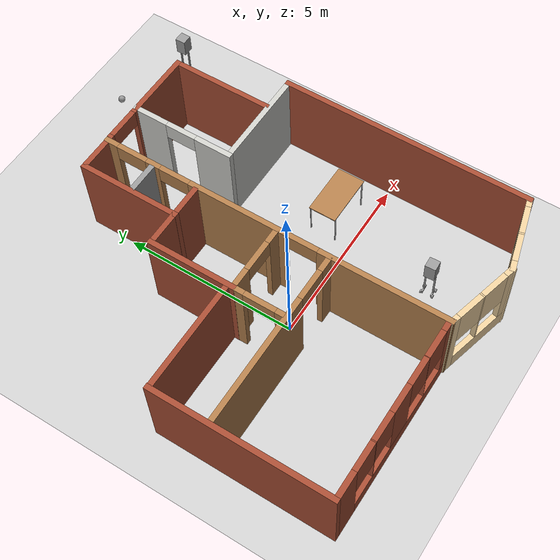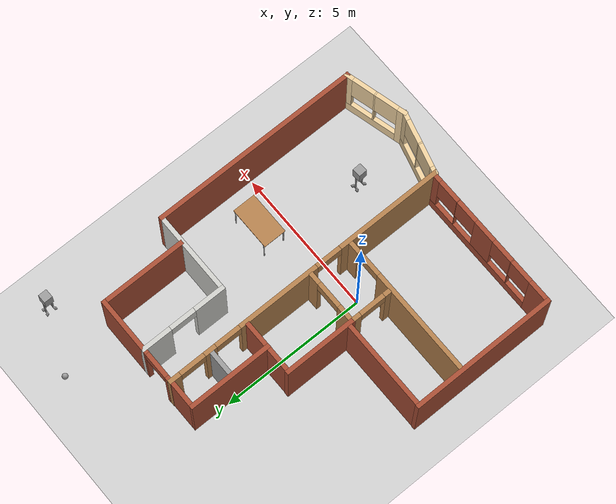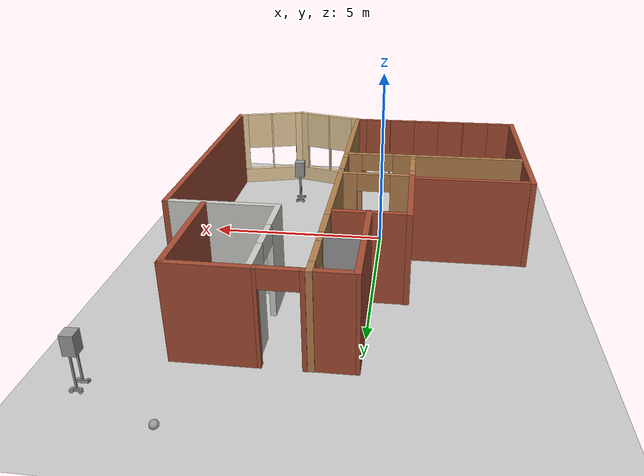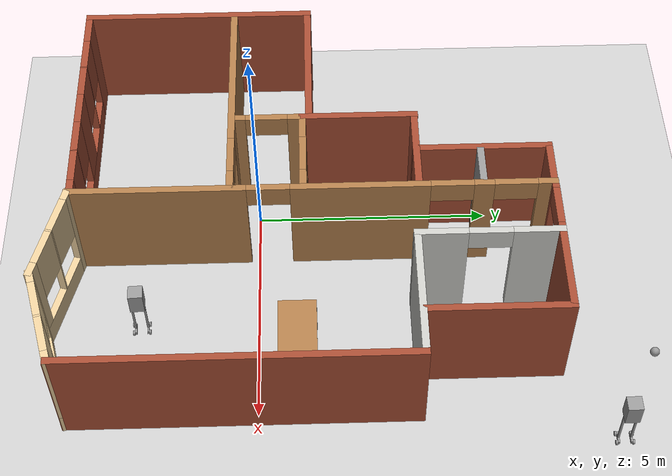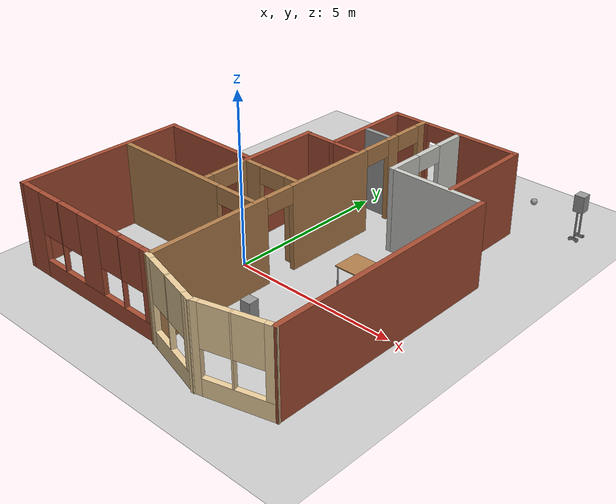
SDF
<sdf version="1.6">
 <world name="default">
  <plugin name="welcome" filename="libwelcome_message.so"/>
  <light name="sun" type="directional">
   <pose>0 0 10 0 -0 0</pose>
   <diffuse>0.8 0.8 0.8 1</diffuse>
   <specular>0.2 0.2 0.2 1</specular>
   <attenuation>
    <range>1000</range>
    <constant>0.9</constant>
    <linear>0.01</linear>
    <quadratic>0.001</quadratic>
   </attenuation>
   <direction>-0.5 0.1 -0.9</direction>
  </light>
  <model name="ground_plane">
   <static>1</static>
   <link name="link">
    <collision name="collision">
     <geometry><plane><normal>0 0 1</normal><size>100 100</size></plane></geometry>
     <surface>
      <contact><collide_bitmask>65535</collide_bitmask></contact>
      <friction><ode><mu>100</mu><mu2>50</mu2></ode></friction>
     </surface>
    </collision>
    <visual name="visual">
     <cast_shadows>0</cast_shadows>
     <geometry><plane><normal>0 0 1</normal><size>100 100</size></plane></geometry>
     <material>
      <script><uri>file://media/materials/scripts/gazebo.material</uri><name>Gazebo/Grey</name></script>
     </material>
    </visual>
   </link>
  </model>
  <gravity>0 0 -9.8</gravity>
  <magnetic_field>6e-06 2.3e-05 -4.2e-05</magnetic_field>
  <atmosphere type="adiabatic"/>
  <physics name="default_physics" default="0" type="ode">
   <max_step_size>0.001</max_step_size>
   <real_time_factor>1</real_time_factor>
   <real_time_update_rate>1000</real_time_update_rate>
  </physics>
  <scene><ambient>0.4 0.4 0.4 1</ambient><background>0.7 0.7 0.7 1</background><shadows>1</shadows></scene>
  <spherical_coordinates>
   <surface_model>EARTH_WGS84</surface_model>
   <latitude_deg>0</latitude_deg>
   <longitude_deg>0</longitude_deg>
   <elevation>0</elevation>
   <heading_deg>0</heading_deg>
  </spherical_coordinates>
  <model name="table">
   <static>1</static>
   <link name="link">
    <collision name="surface">
     <pose>0 0 1 0 -0 0</pose>
     <geometry><box><size>1.5 0.8 0.03</size></box></geometry>
     <surface><friction><ode><mu>0.6</mu><mu2>0.6</mu2></ode></friction></surface>
    </collision>
    <visual name="visual1">
     <pose>0 0 1 0 -0 0</pose>
     <geometry><box><size>1.5 0.8 0.03</size></box></geometry>
     <material>
      <script><uri>file://media/materials/scripts/gazebo.material</uri><name>Gazebo/Wood</name></script>
     </material>
    </visual>
    <collision name="front_left_leg">
     <pose>0.68 0.38 0.5 0 -0 0</pose>
     <geometry><cylinder><radius>0.02</radius><length>1</length></cylinder></geometry>
    </collision>
    <visual name="front_left_leg">
     <pose>0.68 0.38 0.5 0 -0 0</pose>
     <geometry><cylinder><radius>0.02</radius><length>1</length></cylinder></geometry>
     <material>
      <script><uri>file://media/materials/scripts/gazebo.material</uri><name>Gazebo/Grey</name></script>
     </material>
    </visual>
    <collision name="front_right_leg">
     <pose>0.68 -0.38 0.5 0 -0 0</pose>
     <geometry><cylinder><radius>0.02</radius><length>1</length></cylinder></geometry>
    </collision>
    <visual name="front_right_leg">
     <pose>0.68 -0.38 0.5 0 -0 0</pose>
     <geometry><cylinder><radius>0.02</radius><length>1</length></cylinder></geometry>
     <material>
      <script><uri>file://media/materials/scripts/gazebo.material</uri><name>Gazebo/Grey</name></script>
     </material>
    </visual>
    <collision name="back_right_leg">
     <pose>-0.68 -0.38 0.5 0 -0 0</pose>
     <geometry><cylinder><radius>0.02</radius><length>1</length></cylinder></geometry>
    </collision>
    <visual name="back_right_leg">
     <pose>-0.68 -0.38 0.5 0 -0 0</pose>
     <geometry><cylinder><radius>0.02</radius><length>1</length></cylinder></geometry>
     <material>
      <script><uri>file://media/materials/scripts/gazebo.material</uri><name>Gazebo/Grey</name></script>
     </material>
    </visual>
    <collision name="back_left_leg">
     <pose>-0.68 0.38 0.5 0 -0 0</pose>
     <geometry><cylinder><radius>0.02</radius><length>1</length></cylinder></geometry>
    </collision>
    <visual name="back_left_leg">
     <pose>-0.68 0.38 0.5 0 -0 0</pose>
     <geometry><cylinder><radius>0.02</radius><length>1</length></cylinder></geometry>
     <material>
      <script><uri>file://media/materials/scripts/gazebo.material</uri><name>Gazebo/Grey</name></script>
     </material>
    </visual>
   </link>
   <pose>3.63355 0.82495 0 0 -0 0</pose>
  </model>
  <model name="humanoidrobot">
   <link name="link_0">
    <pose>0 -0 0.875556 0 -0 0</pose>
    <inertial>
     <mass>1</mass>
     <inertia>
      <ixx>0.166667</ixx>
      <ixy>0</ixy>
      <ixz>0</ixz>
      <iyy>0.166667</iyy>
      <iyz>0</iyz>
      <izz>0.166667</izz>
     </inertia>
    </inertial>
    <visual name="visual">
     <geometry><box><size>0.3 0.3 0.5</size></box></geometry>
     <material>
      <lighting>1</lighting>
      <script><uri>file://media/materials/scripts/gazebo.material</uri><name>Gazebo/Grey</name></script>
      <shader type="pixel"><normal_map>__default__</normal_map></shader>
      <ambient>0.3 0.3 0.3 1</ambient>
      <diffuse>0.7 0.7 0.7 1</diffuse>
      <specular>0.01 0.01 0.01 1</specular>
      <emissive>0 0 0 1</emissive>
     </material>
    </visual>
    <collision name="collision">
     <geometry><box><size>0.3 0.3 0.5</size></box></geometry>
     <surface>
      <friction>
       <ode><mu>1</mu><mu2>1</mu2><fdir1>0 0 0</fdir1><slip1>0</slip1><slip2>0</slip2></ode>
       <torsional>
        <coefficient>1</coefficient>
        <patch_radius>0</patch_radius>
        <surface_radius>0</surface_radius>
        <use_patch_radius>1</use_patch_radius>
        <ode><slip>0</slip></ode>
       </torsional>
      </friction>
      <bounce><restitution_coefficient>0</restitution_coefficient><threshold>1e+06</threshold></bounce>
      <contact>
       <collide_without_contact>0</collide_without_contact>
       <collide_without_contact_bitmask>1</collide_without_contact_bitmask>
       <collide_bitmask>1</collide_bitmask>
       <ode>
        <soft_cfm>0</soft_cfm>
        <soft_erp>0.2</soft_erp>
        <kp>1e+13</kp>
        <kd>1</kd>
        <max_vel>0.01</max_vel>
        <min_depth>0</min_depth>
       </ode>
       <bullet>
        <split_impulse>1</split_impulse>
        <split_impulse_penetration_threshold>-0.01</split_impulse_penetration_threshold>
        <soft_cfm>0</soft_cfm>
        <soft_erp>0.2</soft_erp>
        <kp>1e+13</kp>
        <kd>1</kd>
       </bullet>
      </contact>
     </surface>
    </collision>
   </link>
   <link name="link_0_clone">
    <pose>0 0.13 0.225556 0 -0 0</pose>
    <inertial>
     <mass>1</mass>
     <inertia>
      <ixx>0.166667</ixx>
      <ixy>0</ixy>
      <ixz>0</ixz>
      <iyy>0.166667</iyy>
      <iyz>0</iyz>
      <izz>0.166667</izz>
     </inertia>
    </inertial>
    <visual name="visual">
     <geometry><box><size>0.04 0.04 0.8</size></box></geometry>
     <material>
      <lighting>1</lighting>
      <script><uri>file://media/materials/scripts/gazebo.material</uri><name>Gazebo/Grey</name></script>
      <shader type="pixel"><normal_map>__default__</normal_map></shader>
      <ambient>0.3 0.3 0.3 1</ambient>
      <diffuse>0.7 0.7 0.7 1</diffuse>
      <specular>0.01 0.01 0.01 1</specular>
      <emissive>0 0 0 1</emissive>
     </material>
    </visual>
    <collision name="collision">
     <geometry><box><size>0.04 0.04 0.8</size></box></geometry>
     <surface>
      <friction>
       <ode><mu>1</mu><mu2>1</mu2><fdir1>0 0 0</fdir1><slip1>0</slip1><slip2>0</slip2></ode>
       <torsional>
        <coefficient>1</coefficient>
        <patch_radius>0</patch_radius>
        <surface_radius>0</surface_radius>
        <use_patch_radius>1</use_patch_radius>
        <ode><slip>0</slip></ode>
       </torsional>
      </friction>
      <bounce><restitution_coefficient>0</restitution_coefficient><threshold>1e+06</threshold></bounce>
      <contact>
       <collide_without_contact>0</collide_without_contact>
       <collide_without_contact_bitmask>1</collide_without_contact_bitmask>
       <collide_bitmask>1</collide_bitmask>
       <ode>
        <soft_cfm>0</soft_cfm>
        <soft_erp>0.2</soft_erp>
        <kp>1e+13</kp>
        <kd>1</kd>
        <max_vel>0.01</max_vel>
        <min_depth>0</min_depth>
       </ode>
       <bullet>
        <split_impulse>1</split_impulse>
        <split_impulse_penetration_threshold>-0.01</split_impulse_penetration_threshold>
        <soft_cfm>0</soft_cfm>
        <soft_erp>0.2</soft_erp>
        <kp>1e+13</kp>
        <kd>1</kd>
       </bullet>
      </contact>
     </surface>
    </collision>
   </link>
   <link name="link_0_clone_clone">
    <pose>-0 -0.13 0.225556 0 -0 0</pose>
    <inertial>
     <mass>1</mass>
     <inertia>
      <ixx>0.166667</ixx>
      <ixy>0</ixy>
      <ixz>0</ixz>
      <iyy>0.166667</iyy>
      <iyz>0</iyz>
      <izz>0.166667</izz>
     </inertia>
    </inertial>
    <visual name="visual">
     <geometry><box><size>0.04 0.04 0.8</size></box></geometry>
     <material>
      <lighting>1</lighting>
      <script><uri>file://media/materials/scripts/gazebo.material</uri><name>Gazebo/Grey</name></script>
      <shader type="pixel"><normal_map>__default__</normal_map></shader>
      <ambient>0.3 0.3 0.3 1</ambient>
      <diffuse>0.7 0.7 0.7 1</diffuse>
      <specular>0.01 0.01 0.01 1</specular>
      <emissive>0 0 0 1</emissive>
     </material>
    </visual>
    <collision name="collision">
     <geometry><box><size>0.04 0.04 0.8</size></box></geometry>
     <surface>
      <friction>
       <ode><mu>1</mu><mu2>1</mu2><fdir1>0 0 0</fdir1><slip1>0</slip1><slip2>0</slip2></ode>
       <torsional>
        <coefficient>1</coefficient>
        <patch_radius>0</patch_radius>
        <surface_radius>0</surface_radius>
        <use_patch_radius>1</use_patch_radius>
        <ode><slip>0</slip></ode>
       </torsional>
      </friction>
      <bounce><restitution_coefficient>0</restitution_coefficient><threshold>1e+06</threshold></bounce>
      <contact>
       <collide_without_contact>0</collide_without_contact>
       <collide_without_contact_bitmask>1</collide_without_contact_bitmask>
       <collide_bitmask>1</collide_bitmask>
       <ode>
        <soft_cfm>0</soft_cfm>
        <soft_erp>0.2</soft_erp>
        <kp>1e+13</kp>
        <kd>1</kd>
        <max_vel>0.01</max_vel>
        <min_depth>0</min_depth>
       </ode>
       <bullet>
        <split_impulse>1</split_impulse>
        <split_impulse_penetration_threshold>-0.01</split_impulse_penetration_threshold>
        <soft_cfm>0</soft_cfm>
        <soft_erp>0.2</soft_erp>
        <kp>1e+13</kp>
        <kd>1</kd>
       </bullet>
      </contact>
     </surface>
    </collision>
   </link>
   <link name="link_1">
    <pose>0 0.13 -0.214444 0 -0 0</pose>
    <inertial>
     <mass>1</mass>
     <inertia>
      <ixx>0.166667</ixx>
      <ixy>0</ixy>
      <ixz>0</ixz>
      <iyy>0.166667</iyy>
      <iyz>0</iyz>
      <izz>0.166667</izz>
     </inertia>
    </inertial>
    <visual name="visual">
     <geometry><box><size>0.24 0.04 0.08</size></box></geometry>
     <material>
      <lighting>1</lighting>
      <script><uri>file://media/materials/scripts/gazebo.material</uri><name>Gazebo/Grey</name></script>
      <shader type="pixel"><normal_map>__default__</normal_map></shader>
      <ambient>0.3 0.3 0.3 1</ambient>
      <diffuse>0.7 0.7 0.7 1</diffuse>
      <specular>0.01 0.01 0.01 1</specular>
      <emissive>0 0 0 1</emissive>
     </material>
    </visual>
    <collision name="collision">
     <geometry><box><size>0.24 0.04 0.08</size></box></geometry>
     <surface>
      <friction>
       <ode><mu>1</mu><mu2>1</mu2><fdir1>0 0 0</fdir1><slip1>0</slip1><slip2>0</slip2></ode>
       <torsional>
        <coefficient>1</coefficient>
        <patch_radius>0</patch_radius>
        <surface_radius>0</surface_radius>
        <use_patch_radius>1</use_patch_radius>
        <ode><slip>0</slip></ode>
       </torsional>
      </friction>
      <bounce><restitution_coefficient>0</restitution_coefficient><threshold>1e+06</threshold></bounce>
      <contact>
       <collide_without_contact>0</collide_without_contact>
       <collide_without_contact_bitmask>1</collide_without_contact_bitmask>
       <collide_bitmask>1</collide_bitmask>
       <ode>
        <soft_cfm>0</soft_cfm>
        <soft_erp>0.2</soft_erp>
        <kp>1e+13</kp>
        <kd>1</kd>
        <max_vel>0.01</max_vel>
        <min_depth>0</min_depth>
       </ode>
       <bullet>
        <split_impulse>1</split_impulse>
        <split_impulse_penetration_threshold>-0.01</split_impulse_penetration_threshold>
        <soft_cfm>0</soft_cfm>
        <soft_erp>0.2</soft_erp>
        <kp>1e+13</kp>
        <kd>1</kd>
       </bullet>
      </contact>
     </surface>
    </collision>
   </link>
   <link name="link_1_clone">
    <pose>-0 -0.13 -0.214444 0 -0 0</pose>
    <inertial>
     <mass>1</mass>
     <inertia>
      <ixx>0.166667</ixx>
      <ixy>0</ixy>
      <ixz>0</ixz>
      <iyy>0.166667</iyy>
      <iyz>0</iyz>
      <izz>0.166667</izz>
     </inertia>
    </inertial>
    <visual name="visual">
     <geometry><box><size>0.24 0.04 0.08</size></box></geometry>
     <material>
      <lighting>1</lighting>
      <script><uri>file://media/materials/scripts/gazebo.material</uri><name>Gazebo/Grey</name></script>
      <shader type="pixel"><normal_map>__default__</normal_map></shader>
      <ambient>0.3 0.3 0.3 1</ambient>
      <diffuse>0.7 0.7 0.7 1</diffuse>
      <specular>0.01 0.01 0.01 1</specular>
      <emissive>0 0 0 1</emissive>
     </material>
    </visual>
    <collision name="collision">
     <geometry><box><size>0.24 0.04 0.08</size></box></geometry>
     <surface>
      <friction>
       <ode><mu>1</mu><mu2>1</mu2><fdir1>0 0 0</fdir1><slip1>0</slip1><slip2>0</slip2></ode>
       <torsional>
        <coefficient>1</coefficient>
        <patch_radius>0</patch_radius>
        <surface_radius>0</surface_radius>
        <use_patch_radius>1</use_patch_radius>
        <ode><slip>0</slip></ode>
       </torsional>
      </friction>
      <bounce><restitution_coefficient>0</restitution_coefficient><threshold>1e+06</threshold></bounce>
      <contact>
       <collide_without_contact>0</collide_without_contact>
       <collide_without_contact_bitmask>1</collide_without_contact_bitmask>
       <collide_bitmask>1</collide_bitmask>
       <ode>
        <soft_cfm>0</soft_cfm>
        <soft_erp>0.2</soft_erp>
        <kp>1e+13</kp>
        <kd>1</kd>
        <max_vel>0.01</max_vel>
        <min_depth>0</min_depth>
       </ode>
       <bullet>
        <split_impulse>1</split_impulse>
        <split_impulse_penetration_threshold>-0.01</split_impulse_penetration_threshold>
        <soft_cfm>0</soft_cfm>
        <soft_erp>0.2</soft_erp>
        <kp>1e+13</kp>
        <kd>1</kd>
       </bullet>
      </contact>
     </surface>
    </collision>
   </link>
   <link name="link_2">
    <pose>0.1 -0.17 -0.224444 1.5707 -0 0</pose>
    <inertial>
     <mass>1</mass>
     <inertia><ixx>0.145833</ixx><ixy>0</ixy><ixz>0</ixz><iyy>0.145833</iyy><iyz>0</iyz><izz>0.125</izz></inertia>
    </inertial>
    <visual name="visual">
     <geometry><cylinder><radius>0.05</radius><length>0.04</length></cylinder></geometry>
     <material>
      <lighting>1</lighting>
      <script><uri>file://media/materials/scripts/gazebo.material</uri><name>Gazebo/Grey</name></script>
      <shader type="pixel"><normal_map>__default__</normal_map></shader>
      <ambient>0.3 0.3 0.3 1</ambient>
      <diffuse>0.7 0.7 0.7 1</diffuse>
      <specular>0.01 0.01 0.01 1</specular>
      <emissive>0 0 0 1</emissive>
     </material>
    </visual>
    <collision name="collision">
     <geometry><cylinder><radius>0.05</radius><length>0.04</length></cylinder></geometry>
     <surface>
      <friction>
       <ode><mu>1</mu><mu2>1</mu2><fdir1>0 0 0</fdir1><slip1>0</slip1><slip2>0</slip2></ode>
       <torsional>
        <coefficient>1</coefficient>
        <patch_radius>0</patch_radius>
        <surface_radius>0</surface_radius>
        <use_patch_radius>1</use_patch_radius>
        <ode><slip>0</slip></ode>
       </torsional>
      </friction>
      <bounce><restitution_coefficient>0</restitution_coefficient><threshold>1e+06</threshold></bounce>
      <contact>
       <collide_without_contact>0</collide_without_contact>
       <collide_without_contact_bitmask>1</collide_without_contact_bitmask>
       <collide_bitmask>1</collide_bitmask>
       <ode>
        <soft_cfm>0</soft_cfm>
        <soft_erp>0.2</soft_erp>
        <kp>1e+13</kp>
        <kd>1</kd>
        <max_vel>0.01</max_vel>
        <min_depth>0</min_depth>
       </ode>
       <bullet>
        <split_impulse>1</split_impulse>
        <split_impulse_penetration_threshold>-0.01</split_impulse_penetration_threshold>
        <soft_cfm>0</soft_cfm>
        <soft_erp>0.2</soft_erp>
        <kp>1e+13</kp>
        <kd>1</kd>
       </bullet>
      </contact>
     </surface>
    </collision>
   </link>
   <link name="link_2_clone">
    <pose>-0.1 -0.17 -0.224444 1.5707 -0 0</pose>
    <inertial>
     <mass>1</mass>
     <inertia><ixx>0.145833</ixx><ixy>0</ixy><ixz>0</ixz><iyy>0.145833</iyy><iyz>0</iyz><izz>0.125</izz></inertia>
    </inertial>
    <visual name="visual">
     <geometry><cylinder><radius>0.05</radius><length>0.04</length></cylinder></geometry>
     <material>
      <lighting>1</lighting>
      <script><uri>file://media/materials/scripts/gazebo.material</uri><name>Gazebo/Grey</name></script>
      <shader type="pixel"><normal_map>__default__</normal_map></shader>
      <ambient>0.3 0.3 0.3 1</ambient>
      <diffuse>0.7 0.7 0.7 1</diffuse>
      <specular>0.01 0.01 0.01 1</specular>
      <emissive>0 0 0 1</emissive>
     </material>
    </visual>
    <collision name="collision">
     <geometry><cylinder><radius>0.05</radius><length>0.04</length></cylinder></geometry>
     <surface>
      <friction>
       <ode><mu>1</mu><mu2>1</mu2><fdir1>0 0 0</fdir1><slip1>0</slip1><slip2>0</slip2></ode>
       <torsional>
        <coefficient>1</coefficient>
        <patch_radius>0</patch_radius>
        <surface_radius>0</surface_radius>
        <use_patch_radius>1</use_patch_radius>
        <ode><slip>0</slip></ode>
       </torsional>
      </friction>
      <bounce><restitution_coefficient>0</restitution_coefficient><threshold>1e+06</threshold></bounce>
      <contact>
       <collide_without_contact>0</collide_without_contact>
       <collide_without_contact_bitmask>1</collide_without_contact_bitmask>
       <collide_bitmask>1</collide_bitmask>
       <ode>
        <soft_cfm>0</soft_cfm>
        <soft_erp>0.2</soft_erp>
        <kp>1e+13</kp>
        <kd>1</kd>
        <max_vel>0.01</max_vel>
        <min_depth>0</min_depth>
       </ode>
       <bullet>
        <split_impulse>1</split_impulse>
        <split_impulse_penetration_threshold>-0.01</split_impulse_penetration_threshold>
        <soft_cfm>0</soft_cfm>
        <soft_erp>0.2</soft_erp>
        <kp>1e+13</kp>
        <kd>1</kd>
       </bullet>
      </contact>
     </surface>
    </collision>
   </link>
   <link name="link_2_clone_0">
    <pose>0.1 0.17 -0.224444 1.5707 -0 0</pose>
    <inertial>
     <mass>1</mass>
     <inertia><ixx>0.145833</ixx><ixy>0</ixy><ixz>0</ixz><iyy>0.145833</iyy><iyz>0</iyz><izz>0.125</izz></inertia>
    </inertial>
    <visual name="visual">
     <geometry><cylinder><radius>0.05</radius><length>0.04</length></cylinder></geometry>
     <material>
      <lighting>1</lighting>
      <script><uri>file://media/materials/scripts/gazebo.material</uri><name>Gazebo/Grey</name></script>
      <shader type="pixel"><normal_map>__default__</normal_map></shader>
      <ambient>0.3 0.3 0.3 1</ambient>
      <diffuse>0.7 0.7 0.7 1</diffuse>
      <specular>0.01 0.01 0.01 1</specular>
      <emissive>0 0 0 1</emissive>
     </material>
    </visual>
    <collision name="collision">
     <geometry><cylinder><radius>0.05</radius><length>0.04</length></cylinder></geometry>
     <surface>
      <friction>
       <ode><mu>1</mu><mu2>1</mu2><fdir1>0 0 0</fdir1><slip1>0</slip1><slip2>0</slip2></ode>
       <torsional>
        <coefficient>1</coefficient>
        <patch_radius>0</patch_radius>
        <surface_radius>0</surface_radius>
        <use_patch_radius>1</use_patch_radius>
        <ode><slip>0</slip></ode>
       </torsional>
      </friction>
      <bounce><restitution_coefficient>0</restitution_coefficient><threshold>1e+06</threshold></bounce>
      <contact>
       <collide_without_contact>0</collide_without_contact>
       <collide_without_contact_bitmask>1</collide_without_contact_bitmask>
       <collide_bitmask>1</collide_bitmask>
       <ode>
        <soft_cfm>0</soft_cfm>
        <soft_erp>0.2</soft_erp>
        <kp>1e+13</kp>
        <kd>1</kd>
        <max_vel>0.01</max_vel>
        <min_depth>0</min_depth>
       </ode>
       <bullet>
        <split_impulse>1</split_impulse>
        <split_impulse_penetration_threshold>-0.01</split_impulse_penetration_threshold>
        <soft_cfm>0</soft_cfm>
        <soft_erp>0.2</soft_erp>
        <kp>1e+13</kp>
        <kd>1</kd>
       </bullet>
      </contact>
     </surface>
    </collision>
   </link>
   <link name="link_2_clone_1">
    <pose>-0.1 0.17 -0.224444 1.5707 -0 0</pose>
    <inertial>
     <mass>1</mass>
     <inertia><ixx>0.145833</ixx><ixy>0</ixy><ixz>0</ixz><iyy>0.145833</iyy><iyz>0</iyz><izz>0.125</izz></inertia>
    </inertial>
    <visual name="visual">
     <geometry><cylinder><radius>0.05</radius><length>0.04</length></cylinder></geometry>
     <material>
      <lighting>1</lighting>
      <script><uri>file://media/materials/scripts/gazebo.material</uri><name>Gazebo/Grey</name></script>
      <shader type="pixel"><normal_map>__default__</normal_map></shader>
      <ambient>0.3 0.3 0.3 1</ambient>
      <diffuse>0.7 0.7 0.7 1</diffuse>
      <specular>0.01 0.01 0.01 1</specular>
      <emissive>0 0 0 1</emissive>
     </material>
    </visual>
    <collision name="collision">
     <geometry><cylinder><radius>0.05</radius><length>0.04</length></cylinder></geometry>
     <surface>
      <friction>
       <ode><mu>1</mu><mu2>1</mu2><fdir1>0 0 0</fdir1><slip1>0</slip1><slip2>0</slip2></ode>
       <torsional>
        <coefficient>1</coefficient>
        <patch_radius>0</patch_radius>
        <surface_radius>0</surface_radius>
        <use_patch_radius>1</use_patch_radius>
        <ode><slip>0</slip></ode>
       </torsional>
      </friction>
      <bounce><restitution_coefficient>0</restitution_coefficient><threshold>1e+06</threshold></bounce>
      <contact>
       <collide_without_contact>0</collide_without_contact>
       <collide_without_contact_bitmask>1</collide_without_contact_bitmask>
       <collide_bitmask>1</collide_bitmask>
       <ode>
        <soft_cfm>0</soft_cfm>
        <soft_erp>0.2</soft_erp>
        <kp>1e+13</kp>
        <kd>1</kd>
        <max_vel>0.01</max_vel>
        <min_depth>0</min_depth>
       </ode>
       <bullet>
        <split_impulse>1</split_impulse>
        <split_impulse_penetration_threshold>-0.01</split_impulse_penetration_threshold>
        <soft_cfm>0</soft_cfm>
        <soft_erp>0.2</soft_erp>
        <kp>1e+13</kp>
        <kd>1</kd>
       </bullet>
      </contact>
     </surface>
    </collision>
   </link>
   <joint name="link_0_JOINT_0" type="fixed">
    <parent>link_0</parent>
    <child>link_0_clone</child>
    <physics>
     <ode><limit><cfm>0</cfm><erp>0.2</erp></limit><suspension><cfm>0</cfm><erp>0.2</erp></suspension></ode>
    </physics>
   </joint>
   <joint name="link_0_JOINT_1" type="fixed">
    <parent>link_0</parent>
    <child>link_0_clone_clone</child>
    <physics>
     <ode><limit><cfm>0</cfm><erp>0.2</erp></limit><suspension><cfm>0</cfm><erp>0.2</erp></suspension></ode>
    </physics>
   </joint>
   <joint name="link_0_clone_JOINT_2" type="fixed">
    <parent>link_0_clone</parent>
    <child>link_1</child>
    <pose>0 0 0 -0.01 0 0</pose>
    <physics>
     <ode><limit><cfm>0</cfm><erp>0.2</erp></limit><suspension><cfm>0</cfm><erp>0.2</erp></suspension></ode>
    </physics>
   </joint>
   <joint name="link_0_clone_clone_JOINT_3" type="fixed">
    <parent>link_0_clone_clone</parent>
    <child>link_1_clone</child>
    <physics>
     <ode><limit><cfm>0</cfm><erp>0.2</erp></limit><suspension><cfm>0</cfm><erp>0.2</erp></suspension></ode>
    </physics>
   </joint>
   <joint name="link_1_JOINT_6" type="revolute">
    <parent>link_1</parent>
    <child>link_2_clone_0</child>
    <axis>
     <xyz>1 0 0</xyz>
     <use_parent_model_frame>0</use_parent_model_frame>
     <limit>
      <lower>-1.79769e+308</lower>
      <upper>1.79769e+308</upper>
      <effort>-1</effort>
      <velocity>-1</velocity>
     </limit>
     <dynamics>
      <spring_reference>0</spring_reference>
      <spring_stiffness>0</spring_stiffness>
      <damping>0</damping>
      <friction>0</friction>
     </dynamics>
    </axis>
    <physics>
     <ode><limit><cfm>0</cfm><erp>0.2</erp></limit><suspension><cfm>0</cfm><erp>0.2</erp></suspension></ode>
    </physics>
   </joint>
   <joint name="link_1_JOINT_7" type="revolute">
    <parent>link_1</parent>
    <child>link_2_clone_1</child>
    <axis>
     <xyz>1 0 0</xyz>
     <use_parent_model_frame>0</use_parent_model_frame>
     <limit>
      <lower>-1.79769e+308</lower>
      <upper>1.79769e+308</upper>
      <effort>-1</effort>
      <velocity>-1</velocity>
     </limit>
     <dynamics>
      <spring_reference>0</spring_reference>
      <spring_stiffness>0</spring_stiffness>
      <damping>0</damping>
      <friction>0</friction>
     </dynamics>
    </axis>
    <physics>
     <ode><limit><cfm>0</cfm><erp>0.2</erp></limit><suspension><cfm>0</cfm><erp>0.2</erp></suspension></ode>
    </physics>
   </joint>
   <joint name="link_1_clone_JOINT_4" type="revolute">
    <parent>link_1_clone</parent>
    <child>link_2</child>
    <axis>
     <xyz>0 0 1</xyz>
     <use_parent_model_frame>0</use_parent_model_frame>
     <limit>
      <lower>-1.79769e+308</lower>
      <upper>1.79769e+308</upper>
      <effort>-1</effort>
      <velocity>-1</velocity>
     </limit>
     <dynamics>
      <spring_reference>0</spring_reference>
      <spring_stiffness>0</spring_stiffness>
      <damping>0</damping>
      <friction>0</friction>
     </dynamics>
    </axis>
    <physics>
     <ode><limit><cfm>0</cfm><erp>0.2</erp></limit><suspension><cfm>0</cfm><erp>0.2</erp></suspension></ode>
    </physics>
   </joint>
   <joint name="link_1_clone_JOINT_5" type="revolute">
    <parent>link_1_clone</parent>
    <child>link_2_clone</child>
    <axis>
     <xyz>0 0 1</xyz>
     <use_parent_model_frame>0</use_parent_model_frame>
     <limit>
      <lower>-1.79769e+308</lower>
      <upper>1.79769e+308</upper>
      <effort>-1</effort>
      <velocity>-1</velocity>
     </limit>
     <dynamics>
      <spring_reference>0</spring_reference>
      <spring_stiffness>0</spring_stiffness>
      <damping>0</damping>
      <friction>0</friction>
     </dynamics>
    </axis>
    <physics>
     <ode><limit><cfm>0</cfm><erp>0.2</erp></limit><suspension><cfm>0</cfm><erp>0.2</erp></suspension></ode>
    </physics>
   </joint>
   <static>0</static>
   <pose>5.75235 7.31214 0.274445 -1.7e-05 1.1e-05 0.008436</pose>
  </model>
  <model name="humanoidrobot_0">
   <link name="link_0">
    <pose>0 -0 0.875556 0 -0 0</pose>
    <inertial>
     <mass>1</mass>
     <inertia>
      <ixx>0.166667</ixx>
      <ixy>0</ixy>
      <ixz>0</ixz>
      <iyy>0.166667</iyy>
      <iyz>0</iyz>
      <izz>0.166667</izz>
     </inertia>
    </inertial>
    <visual name="visual">
     <geometry><box><size>0.3 0.3 0.5</size></box></geometry>
     <material>
      <lighting>1</lighting>
      <script><uri>file://media/materials/scripts/gazebo.material</uri><name>Gazebo/Grey</name></script>
      <shader type="pixel"><normal_map>__default__</normal_map></shader>
      <ambient>0.3 0.3 0.3 1</ambient>
      <diffuse>0.7 0.7 0.7 1</diffuse>
      <specular>0.01 0.01 0.01 1</specular>
      <emissive>0 0 0 1</emissive>
     </material>
    </visual>
    <collision name="collision">
     <geometry><box><size>0.3 0.3 0.5</size></box></geometry>
     <surface>
      <friction>
       <ode><mu>1</mu><mu2>1</mu2><fdir1>0 0 0</fdir1><slip1>0</slip1><slip2>0</slip2></ode>
       <torsional>
        <coefficient>1</coefficient>
        <patch_radius>0</patch_radius>
        <surface_radius>0</surface_radius>
        <use_patch_radius>1</use_patch_radius>
        <ode><slip>0</slip></ode>
       </torsional>
      </friction>
      <bounce><restitution_coefficient>0</restitution_coefficient><threshold>1e+06</threshold></bounce>
      <contact>
       <collide_without_contact>0</collide_without_contact>
       <collide_without_contact_bitmask>1</collide_without_contact_bitmask>
       <collide_bitmask>1</collide_bitmask>
       <ode>
        <soft_cfm>0</soft_cfm>
        <soft_erp>0.2</soft_erp>
        <kp>1e+13</kp>
        <kd>1</kd>
        <max_vel>0.01</max_vel>
        <min_depth>0</min_depth>
       </ode>
       <bullet>
        <split_impulse>1</split_impulse>
        <split_impulse_penetration_threshold>-0.01</split_impulse_penetration_threshold>
        <soft_cfm>0</soft_cfm>
        <soft_erp>0.2</soft_erp>
        <kp>1e+13</kp>
        <kd>1</kd>
       </bullet>
      </contact>
     </surface>
    </collision>
   </link>
   <link name="link_0_clone">
    <pose>0 0.13 0.225556 0 -0 0</pose>
    <inertial>
     <mass>1</mass>
     <inertia>
      <ixx>0.166667</ixx>
      <ixy>0</ixy>
      <ixz>0</ixz>
      <iyy>0.166667</iyy>
      <iyz>0</iyz>
      <izz>0.166667</izz>
     </inertia>
    </inertial>
    <visual name="visual">
     <geometry><box><size>0.04 0.04 0.8</size></box></geometry>
     <material>
      <lighting>1</lighting>
      <script><uri>file://media/materials/scripts/gazebo.material</uri><name>Gazebo/Grey</name></script>
      <shader type="pixel"><normal_map>__default__</normal_map></shader>
      <ambient>0.3 0.3 0.3 1</ambient>
      <diffuse>0.7 0.7 0.7 1</diffuse>
      <specular>0.01 0.01 0.01 1</specular>
      <emissive>0 0 0 1</emissive>
     </material>
    </visual>
    <collision name="collision">
     <geometry><box><size>0.04 0.04 0.8</size></box></geometry>
     <surface>
      <friction>
       <ode><mu>1</mu><mu2>1</mu2><fdir1>0 0 0</fdir1><slip1>0</slip1><slip2>0</slip2></ode>
       <torsional>
        <coefficient>1</coefficient>
        <patch_radius>0</patch_radius>
        <surface_radius>0</surface_radius>
        <use_patch_radius>1</use_patch_radius>
        <ode><slip>0</slip></ode>
       </torsional>
      </friction>
      <bounce><restitution_coefficient>0</restitution_coefficient><threshold>1e+06</threshold></bounce>
      <contact>
       <collide_without_contact>0</collide_without_contact>
       <collide_without_contact_bitmask>1</collide_without_contact_bitmask>
       <collide_bitmask>1</collide_bitmask>
       <ode>
        <soft_cfm>0</soft_cfm>
        <soft_erp>0.2</soft_erp>
        <kp>1e+13</kp>
        <kd>1</kd>
        <max_vel>0.01</max_vel>
        <min_depth>0</min_depth>
       </ode>
       <bullet>
        <split_impulse>1</split_impulse>
        <split_impulse_penetration_threshold>-0.01</split_impulse_penetration_threshold>
        <soft_cfm>0</soft_cfm>
        <soft_erp>0.2</soft_erp>
        <kp>1e+13</kp>
        <kd>1</kd>
       </bullet>
      </contact>
     </surface>
    </collision>
   </link>
   <link name="link_0_clone_clone">
    <pose>-0 -0.13 0.225556 0 -0 0</pose>
    <inertial>
     <mass>1</mass>
     <inertia>
      <ixx>0.166667</ixx>
      <ixy>0</ixy>
      <ixz>0</ixz>
      <iyy>0.166667</iyy>
      <iyz>0</iyz>
      <izz>0.166667</izz>
     </inertia>
    </inertial>
    <visual name="visual">
     <geometry><box><size>0.04 0.04 0.8</size></box></geometry>
     <material>
      <lighting>1</lighting>
      <script><uri>file://media/materials/scripts/gazebo.material</uri><name>Gazebo/Grey</name></script>
      <shader type="pixel"><normal_map>__default__</normal_map></shader>
      <ambient>0.3 0.3 0.3 1</ambient>
      <diffuse>0.7 0.7 0.7 1</diffuse>
      <specular>0.01 0.01 0.01 1</specular>
      <emissive>0 0 0 1</emissive>
     </material>
    </visual>
    <collision name="collision">
     <geometry><box><size>0.04 0.04 0.8</size></box></geometry>
     <surface>
      <friction>
       <ode><mu>1</mu><mu2>1</mu2><fdir1>0 0 0</fdir1><slip1>0</slip1><slip2>0</slip2></ode>
       <torsional>
        <coefficient>1</coefficient>
        <patch_radius>0</patch_radius>
        <surface_radius>0</surface_radius>
        <use_patch_radius>1</use_patch_radius>
        <ode><slip>0</slip></ode>
       </torsional>
      </friction>
      <bounce><restitution_coefficient>0</restitution_coefficient><threshold>1e+06</threshold></bounce>
      <contact>
       <collide_without_contact>0</collide_without_contact>
       <collide_without_contact_bitmask>1</collide_without_contact_bitmask>
       <collide_bitmask>1</collide_bitmask>
       <ode>
        <soft_cfm>0</soft_cfm>
        <soft_erp>0.2</soft_erp>
        <kp>1e+13</kp>
        <kd>1</kd>
        <max_vel>0.01</max_vel>
        <min_depth>0</min_depth>
       </ode>
       <bullet>
        <split_impulse>1</split_impulse>
        <split_impulse_penetration_threshold>-0.01</split_impulse_penetration_threshold>
        <soft_cfm>0</soft_cfm>
        <soft_erp>0.2</soft_erp>
        <kp>1e+13</kp>
        <kd>1</kd>
       </bullet>
      </contact>
     </surface>
    </collision>
   </link>
   <link name="link_1">
    <pose>0 0.13 -0.214444 0 -0 0</pose>
    <inertial>
     <mass>1</mass>
     <inertia>
      <ixx>0.166667</ixx>
      <ixy>0</ixy>
      <ixz>0</ixz>
      <iyy>0.166667</iyy>
      <iyz>0</iyz>
      <izz>0.166667</izz>
     </inertia>
    </inertial>
    <visual name="visual">
     <geometry><box><size>0.24 0.04 0.08</size></box></geometry>
     <material>
      <lighting>1</lighting>
      <script><uri>file://media/materials/scripts/gazebo.material</uri><name>Gazebo/Grey</name></script>
      <shader type="pixel"><normal_map>__default__</normal_map></shader>
      <ambient>0.3 0.3 0.3 1</ambient>
      <diffuse>0.7 0.7 0.7 1</diffuse>
      <specular>0.01 0.01 0.01 1</specular>
      <emissive>0 0 0 1</emissive>
     </material>
    </visual>
    <collision name="collision">
     <geometry><box><size>0.24 0.04 0.08</size></box></geometry>
     <surface>
      <friction>
       <ode><mu>1</mu><mu2>1</mu2><fdir1>0 0 0</fdir1><slip1>0</slip1><slip2>0</slip2></ode>
       <torsional>
        <coefficient>1</coefficient>
        <patch_radius>0</patch_radius>
        <surface_radius>0</surface_radius>
        <use_patch_radius>1</use_patch_radius>
        <ode><slip>0</slip></ode>
       </torsional>
      </friction>
      <bounce><restitution_coefficient>0</restitution_coefficient><threshold>1e+06</threshold></bounce>
      <contact>
       <collide_without_contact>0</collide_without_contact>
       <collide_without_contact_bitmask>1</collide_without_contact_bitmask>
       <collide_bitmask>1</collide_bitmask>
       <ode>
        <soft_cfm>0</soft_cfm>
        <soft_erp>0.2</soft_erp>
        <kp>1e+13</kp>
        <kd>1</kd>
        <max_vel>0.01</max_vel>
        <min_depth>0</min_depth>
       </ode>
       <bullet>
        <split_impulse>1</split_impulse>
        <split_impulse_penetration_threshold>-0.01</split_impulse_penetration_threshold>
        <soft_cfm>0</soft_cfm>
        <soft_erp>0.2</soft_erp>
        <kp>1e+13</kp>
        <kd>1</kd>
       </bullet>
      </contact>
     </surface>
    </collision>
   </link>
   <link name="link_1_clone">
    <pose>-0 -0.13 -0.214444 0 -0 0</pose>
    <inertial>
     <mass>1</mass>
     <inertia>
      <ixx>0.166667</ixx>
      <ixy>0</ixy>
      <ixz>0</ixz>
      <iyy>0.166667</iyy>
      <iyz>0</iyz>
      <izz>0.166667</izz>
     </inertia>
    </inertial>
    <visual name="visual">
     <geometry><box><size>0.24 0.04 0.08</size></box></geometry>
     <material>
      <lighting>1</lighting>
      <script><uri>file://media/materials/scripts/gazebo.material</uri><name>Gazebo/Grey</name></script>
      <shader type="pixel"><normal_map>__default__</normal_map></shader>
      <ambient>0.3 0.3 0.3 1</ambient>
      <diffuse>0.7 0.7 0.7 1</diffuse>
      <specular>0.01 0.01 0.01 1</specular>
      <emissive>0 0 0 1</emissive>
     </material>
    </visual>
    <collision name="collision">
     <geometry><box><size>0.24 0.04 0.08</size></box></geometry>
     <surface>
      <friction>
       <ode><mu>1</mu><mu2>1</mu2><fdir1>0 0 0</fdir1><slip1>0</slip1><slip2>0</slip2></ode>
       <torsional>
        <coefficient>1</coefficient>
        <patch_radius>0</patch_radius>
        <surface_radius>0</surface_radius>
        <use_patch_radius>1</use_patch_radius>
        <ode><slip>0</slip></ode>
       </torsional>
      </friction>
      <bounce><restitution_coefficient>0</restitution_coefficient><threshold>1e+06</threshold></bounce>
      <contact>
       <collide_without_contact>0</collide_without_contact>
       <collide_without_contact_bitmask>1</collide_without_contact_bitmask>
       <collide_bitmask>1</collide_bitmask>
       <ode>
        <soft_cfm>0</soft_cfm>
        <soft_erp>0.2</soft_erp>
        <kp>1e+13</kp>
        <kd>1</kd>
        <max_vel>0.01</max_vel>
        <min_depth>0</min_depth>
       </ode>
       <bullet>
        <split_impulse>1</split_impulse>
        <split_impulse_penetration_threshold>-0.01</split_impulse_penetration_threshold>
        <soft_cfm>0</soft_cfm>
        <soft_erp>0.2</soft_erp>
        <kp>1e+13</kp>
        <kd>1</kd>
       </bullet>
      </contact>
     </surface>
    </collision>
   </link>
   <link name="link_2">
    <pose>0.1 -0.17 -0.224444 1.5707 -0 0</pose>
    <inertial>
     <mass>1</mass>
     <inertia><ixx>0.145833</ixx><ixy>0</ixy><ixz>0</ixz><iyy>0.145833</iyy><iyz>0</iyz><izz>0.125</izz></inertia>
    </inertial>
    <visual name="visual">
     <geometry><cylinder><radius>0.05</radius><length>0.04</length></cylinder></geometry>
     <material>
      <lighting>1</lighting>
      <script><uri>file://media/materials/scripts/gazebo.material</uri><name>Gazebo/Grey</name></script>
      <shader type="pixel"><normal_map>__default__</normal_map></shader>
      <ambient>0.3 0.3 0.3 1</ambient>
      <diffuse>0.7 0.7 0.7 1</diffuse>
      <specular>0.01 0.01 0.01 1</specular>
      <emissive>0 0 0 1</emissive>
     </material>
    </visual>
    <collision name="collision">
     <geometry><cylinder><radius>0.05</radius><length>0.04</length></cylinder></geometry>
     <surface>
      <friction>
       <ode><mu>1</mu><mu2>1</mu2><fdir1>0 0 0</fdir1><slip1>0</slip1><slip2>0</slip2></ode>
       <torsional>
        <coefficient>1</coefficient>
        <patch_radius>0</patch_radius>
        <surface_radius>0</surface_radius>
        <use_patch_radius>1</use_patch_radius>
        <ode><slip>0</slip></ode>
       </torsional>
      </friction>
      <bounce><restitution_coefficient>0</restitution_coefficient><threshold>1e+06</threshold></bounce>
      <contact>
       <collide_without_contact>0</collide_without_contact>
       <collide_without_contact_bitmask>1</collide_without_contact_bitmask>
       <collide_bitmask>1</collide_bitmask>
       <ode>
        <soft_cfm>0</soft_cfm>
        <soft_erp>0.2</soft_erp>
        <kp>1e+13</kp>
        <kd>1</kd>
        <max_vel>0.01</max_vel>
        <min_depth>0</min_depth>
       </ode>
       <bullet>
        <split_impulse>1</split_impulse>
        <split_impulse_penetration_threshold>-0.01</split_impulse_penetration_threshold>
        <soft_cfm>0</soft_cfm>
        <soft_erp>0.2</soft_erp>
        <kp>1e+13</kp>
        <kd>1</kd>
       </bullet>
      </contact>
     </surface>
    </collision>
   </link>
   <link name="link_2_clone">
    <pose>-0.1 -0.17 -0.224444 1.5707 -0 0</pose>
    <inertial>
     <mass>1</mass>
     <inertia><ixx>0.145833</ixx><ixy>0</ixy><ixz>0</ixz><iyy>0.145833</iyy><iyz>0</iyz><izz>0.125</izz></inertia>
    </inertial>
    <visual name="visual">
     <geometry><cylinder><radius>0.05</radius><length>0.04</length></cylinder></geometry>
     <material>
      <lighting>1</lighting>
      <script><uri>file://media/materials/scripts/gazebo.material</uri><name>Gazebo/Grey</name></script>
      <shader type="pixel"><normal_map>__default__</normal_map></shader>
      <ambient>0.3 0.3 0.3 1</ambient>
      <diffuse>0.7 0.7 0.7 1</diffuse>
      <specular>0.01 0.01 0.01 1</specular>
      <emissive>0 0 0 1</emissive>
     </material>
    </visual>
    <collision name="collision">
     <geometry><cylinder><radius>0.05</radius><length>0.04</length></cylinder></geometry>
     <surface>
      <friction>
       <ode><mu>1</mu><mu2>1</mu2><fdir1>0 0 0</fdir1><slip1>0</slip1><slip2>0</slip2></ode>
       <torsional>
        <coefficient>1</coefficient>
        <patch_radius>0</patch_radius>
        <surface_radius>0</surface_radius>
        <use_patch_radius>1</use_patch_radius>
        <ode><slip>0</slip></ode>
       </torsional>
      </friction>
      <bounce><restitution_coefficient>0</restitution_coefficient><threshold>1e+06</threshold></bounce>
      <contact>
       <collide_without_contact>0</collide_without_contact>
       <collide_without_contact_bitmask>1</collide_without_contact_bitmask>
       <collide_bitmask>1</collide_bitmask>
       <ode>
        <soft_cfm>0</soft_cfm>
        <soft_erp>0.2</soft_erp>
        <kp>1e+13</kp>
        <kd>1</kd>
        <max_vel>0.01</max_vel>
        <min_depth>0</min_depth>
       </ode>
       <bullet>
        <split_impulse>1</split_impulse>
        <split_impulse_penetration_threshold>-0.01</split_impulse_penetration_threshold>
        <soft_cfm>0</soft_cfm>
        <soft_erp>0.2</soft_erp>
        <kp>1e+13</kp>
        <kd>1</kd>
       </bullet>
      </contact>
     </surface>
    </collision>
   </link>
   <link name="link_2_clone_0">
    <pose>0.1 0.17 -0.224444 1.5707 -0 0</pose>
    <inertial>
     <mass>1</mass>
     <inertia><ixx>0.145833</ixx><ixy>0</ixy><ixz>0</ixz><iyy>0.145833</iyy><iyz>0</iyz><izz>0.125</izz></inertia>
    </inertial>
    <visual name="visual">
     <geometry><cylinder><radius>0.05</radius><length>0.04</length></cylinder></geometry>
     <material>
      <lighting>1</lighting>
      <script><uri>file://media/materials/scripts/gazebo.material</uri><name>Gazebo/Grey</name></script>
      <shader type="pixel"><normal_map>__default__</normal_map></shader>
      <ambient>0.3 0.3 0.3 1</ambient>
      <diffuse>0.7 0.7 0.7 1</diffuse>
      <specular>0.01 0.01 0.01 1</specular>
      <emissive>0 0 0 1</emissive>
     </material>
    </visual>
    <collision name="collision">
     <geometry><cylinder><radius>0.05</radius><length>0.04</length></cylinder></geometry>
     <surface>
      <friction>
       <ode><mu>1</mu><mu2>1</mu2><fdir1>0 0 0</fdir1><slip1>0</slip1><slip2>0</slip2></ode>
       <torsional>
        <coefficient>1</coefficient>
        <patch_radius>0</patch_radius>
        <surface_radius>0</surface_radius>
        <use_patch_radius>1</use_patch_radius>
        <ode><slip>0</slip></ode>
       </torsional>
      </friction>
      <bounce><restitution_coefficient>0</restitution_coefficient><threshold>1e+06</threshold></bounce>
      <contact>
       <collide_without_contact>0</collide_without_contact>
       <collide_without_contact_bitmask>1</collide_without_contact_bitmask>
       <collide_bitmask>1</collide_bitmask>
       <ode>
        <soft_cfm>0</soft_cfm>
        <soft_erp>0.2</soft_erp>
        <kp>1e+13</kp>
        <kd>1</kd>
        <max_vel>0.01</max_vel>
        <min_depth>0</min_depth>
       </ode>
       <bullet>
        <split_impulse>1</split_impulse>
        <split_impulse_penetration_threshold>-0.01</split_impulse_penetration_threshold>
        <soft_cfm>0</soft_cfm>
        <soft_erp>0.2</soft_erp>
        <kp>1e+13</kp>
        <kd>1</kd>
       </bullet>
      </contact>
     </surface>
    </collision>
   </link>
   <link name="link_2_clone_1">
    <pose>-0.1 0.17 -0.224444 1.5707 -0 0</pose>
    <inertial>
     <mass>1</mass>
     <inertia><ixx>0.145833</ixx><ixy>0</ixy><ixz>0</ixz><iyy>0.145833</iyy><iyz>0</iyz><izz>0.125</izz></inertia>
    </inertial>
    <visual name="visual">
     <geometry><cylinder><radius>0.05</radius><length>0.04</length></cylinder></geometry>
     <material>
      <lighting>1</lighting>
      <script><uri>file://media/materials/scripts/gazebo.material</uri><name>Gazebo/Grey</name></script>
      <shader type="pixel"><normal_map>__default__</normal_map></shader>
      <ambient>0.3 0.3 0.3 1</ambient>
      <diffuse>0.7 0.7 0.7 1</diffuse>
      <specular>0.01 0.01 0.01 1</specular>
      <emissive>0 0 0 1</emissive>
     </material>
    </visual>
    <collision name="collision">
     <geometry><cylinder><radius>0.05</radius><length>0.04</length></cylinder></geometry>
     <surface>
      <friction>
       <ode><mu>1</mu><mu2>1</mu2><fdir1>0 0 0</fdir1><slip1>0</slip1><slip2>0</slip2></ode>
       <torsional>
        <coefficient>1</coefficient>
        <patch_radius>0</patch_radius>
        <surface_radius>0</surface_radius>
        <use_patch_radius>1</use_patch_radius>
        <ode><slip>0</slip></ode>
       </torsional>
      </friction>
      <bounce><restitution_coefficient>0</restitution_coefficient><threshold>1e+06</threshold></bounce>
      <contact>
       <collide_without_contact>0</collide_without_contact>
       <collide_without_contact_bitmask>1</collide_without_contact_bitmask>
       <collide_bitmask>1</collide_bitmask>
       <ode>
        <soft_cfm>0</soft_cfm>
        <soft_erp>0.2</soft_erp>
        <kp>1e+13</kp>
        <kd>1</kd>
        <max_vel>0.01</max_vel>
        <min_depth>0</min_depth>
       </ode>
       <bullet>
        <split_impulse>1</split_impulse>
        <split_impulse_penetration_threshold>-0.01</split_impulse_penetration_threshold>
        <soft_cfm>0</soft_cfm>
        <soft_erp>0.2</soft_erp>
        <kp>1e+13</kp>
        <kd>1</kd>
       </bullet>
      </contact>
     </surface>
    </collision>
   </link>
   <joint name="link_0_JOINT_0" type="fixed">
    <parent>link_0</parent>
    <child>link_0_clone</child>
    <physics>
     <ode><limit><cfm>0</cfm><erp>0.2</erp></limit><suspension><cfm>0</cfm><erp>0.2</erp></suspension></ode>
    </physics>
   </joint>
   <joint name="link_0_JOINT_1" type="fixed">
    <parent>link_0</parent>
    <child>link_0_clone_clone</child>
    <physics>
     <ode><limit><cfm>0</cfm><erp>0.2</erp></limit><suspension><cfm>0</cfm><erp>0.2</erp></suspension></ode>
    </physics>
   </joint>
   <joint name="link_0_clone_JOINT_2" type="fixed">
    <parent>link_0_clone</parent>
    <child>link_1</child>
    <pose>0 0 0 -0.01 0 0</pose>
    <physics>
     <ode><limit><cfm>0</cfm><erp>0.2</erp></limit><suspension><cfm>0</cfm><erp>0.2</erp></suspension></ode>
    </physics>
   </joint>
   <joint name="link_0_clone_clone_JOINT_3" type="fixed">
    <parent>link_0_clone_clone</parent>
    <child>link_1_clone</child>
    <physics>
     <ode><limit><cfm>0</cfm><erp>0.2</erp></limit><suspension><cfm>0</cfm><erp>0.2</erp></suspension></ode>
    </physics>
   </joint>
   <joint name="link_1_JOINT_6" type="revolute">
    <parent>link_1</parent>
    <child>link_2_clone_0</child>
    <axis>
     <xyz>1 0 0</xyz>
     <use_parent_model_frame>0</use_parent_model_frame>
     <limit>
      <lower>-1.79769e+308</lower>
      <upper>1.79769e+308</upper>
      <effort>-1</effort>
      <velocity>-1</velocity>
     </limit>
     <dynamics>
      <spring_reference>0</spring_reference>
      <spring_stiffness>0</spring_stiffness>
      <damping>0</damping>
      <friction>0</friction>
     </dynamics>
    </axis>
    <physics>
     <ode><limit><cfm>0</cfm><erp>0.2</erp></limit><suspension><cfm>0</cfm><erp>0.2</erp></suspension></ode>
    </physics>
   </joint>
   <joint name="link_1_JOINT_7" type="revolute">
    <parent>link_1</parent>
    <child>link_2_clone_1</child>
    <axis>
     <xyz>1 0 0</xyz>
     <use_parent_model_frame>0</use_parent_model_frame>
     <limit>
      <lower>-1.79769e+308</lower>
      <upper>1.79769e+308</upper>
      <effort>-1</effort>
      <velocity>-1</velocity>
     </limit>
     <dynamics>
      <spring_reference>0</spring_reference>
      <spring_stiffness>0</spring_stiffness>
      <damping>0</damping>
      <friction>0</friction>
     </dynamics>
    </axis>
    <physics>
     <ode><limit><cfm>0</cfm><erp>0.2</erp></limit><suspension><cfm>0</cfm><erp>0.2</erp></suspension></ode>
    </physics>
   </joint>
   <joint name="link_1_clone_JOINT_4" type="revolute">
    <parent>link_1_clone</parent>
    <child>link_2</child>
    <axis>
     <xyz>0 0 1</xyz>
     <use_parent_model_frame>0</use_parent_model_frame>
     <limit>
      <lower>-1.79769e+308</lower>
      <upper>1.79769e+308</upper>
      <effort>-1</effort>
      <velocity>-1</velocity>
     </limit>
     <dynamics>
      <spring_reference>0</spring_reference>
      <spring_stiffness>0</spring_stiffness>
      <damping>0</damping>
      <friction>0</friction>
     </dynamics>
    </axis>
    <physics>
     <ode><limit><cfm>0</cfm><erp>0.2</erp></limit><suspension><cfm>0</cfm><erp>0.2</erp></suspension></ode>
    </physics>
   </joint>
   <joint name="link_1_clone_JOINT_5" type="revolute">
    <parent>link_1_clone</parent>
    <child>link_2_clone</child>
    <axis>
     <xyz>0 0 1</xyz>
     <use_parent_model_frame>0</use_parent_model_frame>
     <limit>
      <lower>-1.79769e+308</lower>
      <upper>1.79769e+308</upper>
      <effort>-1</effort>
      <velocity>-1</velocity>
     </limit>
     <dynamics>
      <spring_reference>0</spring_reference>
      <spring_stiffness>0</spring_stiffness>
      <damping>0</damping>
      <friction>0</friction>
     </dynamics>
    </axis>
    <physics>
     <ode><limit><cfm>0</cfm><erp>0.2</erp></limit><suspension><cfm>0</cfm><erp>0.2</erp></suspension></ode>
    </physics>
   </joint>
   <static>0</static>
   <pose>2.8527 -2.4732 0.274438 -1.1e-05 2e-06 0.048587</pose>
  </model>
  <model name="building">
   <link name="Wall_0">
    <pose>1.13831 5.31811 0 0 -0 0</pose>
    <visual name="Wall_0_Visual_2">
     <pose>0.011315 0 2.25 0 -0 0</pose>
     <geometry><box><size>0.9 0.15 0.5</size></box></geometry>
     <material>
      <script><uri>file://media/materials/scripts/gazebo.material</uri><name>Gazebo/Bricks</name></script>
      <ambient>1 1 1 1</ambient>
      <shader type="pixel"/>
      <diffuse>1 1 1 1</diffuse>
      <specular>0.2 0.2 0.2 1</specular>
      <emissive>0 0 0 1</emissive>
     </material>
     <meta><layer>0</layer></meta>
    </visual>
    <visual name="Wall_0_Visual_1">
     <pose>0.504908 0 1.25 0 -0 0</pose>
     <geometry><box><size>0.087185 0.15 2.5</size></box></geometry>
     <material>
      <script><uri>file://media/materials/scripts/gazebo.material</uri><name>Gazebo/Bricks</name></script>
      <ambient>1 1 1 1</ambient>
      <shader type="pixel"/>
      <diffuse>1 1 1 1</diffuse>
      <specular>0.2 0.2 0.2 1</specular>
      <emissive>0 0 0 1</emissive>
     </material>
     <meta><layer>0</layer></meta>
    </visual>
    <visual name="Wall_0_Visual_0">
     <pose>-0.493592 0 1.25 0 -0 0</pose>
     <geometry><box><size>0.109815 0.15 2.5</size></box></geometry>
     <material>
      <script><uri>file://media/materials/scripts/gazebo.material</uri><name>Gazebo/Bricks</name></script>
      <ambient>1 1 1 1</ambient>
      <shader type="pixel"/>
      <diffuse>1 1 1 1</diffuse>
      <specular>0.2 0.2 0.2 1</specular>
      <emissive>0 0 0 1</emissive>
     </material>
     <meta><layer>0</layer></meta>
    </visual>
    <collision name="Wall_0_Collision_1">
     <pose>0.504908 0 1.25 0 -0 0</pose>
     <geometry><box><size>0.087185 0.15 2.5</size></box></geometry>
     <surface>
      <friction>
       <ode><mu>1</mu><mu2>1</mu2><fdir1>0 0 0</fdir1><slip1>0</slip1><slip2>0</slip2></ode>
       <torsional>
        <coefficient>1</coefficient>
        <patch_radius>0</patch_radius>
        <surface_radius>0</surface_radius>
        <use_patch_radius>1</use_patch_radius>
        <ode><slip>0</slip></ode>
       </torsional>
      </friction>
      <bounce><restitution_coefficient>0</restitution_coefficient><threshold>1e+06</threshold></bounce>
      <contact>
       <collide_without_contact>0</collide_without_contact>
       <collide_without_contact_bitmask>1</collide_without_contact_bitmask>
       <collide_bitmask>1</collide_bitmask>
       <ode>
        <soft_cfm>0</soft_cfm>
        <soft_erp>0.2</soft_erp>
        <kp>1e+13</kp>
        <kd>1</kd>
        <max_vel>0.01</max_vel>
        <min_depth>0</min_depth>
       </ode>
       <bullet>
        <split_impulse>1</split_impulse>
        <split_impulse_penetration_threshold>-0.01</split_impulse_penetration_threshold>
        <soft_cfm>0</soft_cfm>
        <soft_erp>0.2</soft_erp>
        <kp>1e+13</kp>
        <kd>1</kd>
       </bullet>
      </contact>
     </surface>
    </collision>
    <collision name="Wall_0_Collision_2">
     <pose>0.011315 0 2.25 0 -0 0</pose>
     <geometry><box><size>0.9 0.15 0.5</size></box></geometry>
     <surface>
      <friction>
       <ode><mu>1</mu><mu2>1</mu2><fdir1>0 0 0</fdir1><slip1>0</slip1><slip2>0</slip2></ode>
       <torsional>
        <coefficient>1</coefficient>
        <patch_radius>0</patch_radius>
        <surface_radius>0</surface_radius>
        <use_patch_radius>1</use_patch_radius>
        <ode><slip>0</slip></ode>
       </torsional>
      </friction>
      <bounce><restitution_coefficient>0</restitution_coefficient><threshold>1e+06</threshold></bounce>
      <contact>
       <collide_without_contact>0</collide_without_contact>
       <collide_without_contact_bitmask>1</collide_without_contact_bitmask>
       <collide_bitmask>1</collide_bitmask>
       <ode>
        <soft_cfm>0</soft_cfm>
        <soft_erp>0.2</soft_erp>
        <kp>1e+13</kp>
        <kd>1</kd>
        <max_vel>0.01</max_vel>
        <min_depth>0</min_depth>
       </ode>
       <bullet>
        <split_impulse>1</split_impulse>
        <split_impulse_penetration_threshold>-0.01</split_impulse_penetration_threshold>
        <soft_cfm>0</soft_cfm>
        <soft_erp>0.2</soft_erp>
        <kp>1e+13</kp>
        <kd>1</kd>
       </bullet>
      </contact>
     </surface>
    </collision>
    <collision name="Wall_0_Collision_0">
     <pose>-0.493592 0 1.25 0 -0 0</pose>
     <geometry><box><size>0.109815 0.15 2.5</size></box></geometry>
     <surface>
      <friction>
       <ode><mu>1</mu><mu2>1</mu2><fdir1>0 0 0</fdir1><slip1>0</slip1><slip2>0</slip2></ode>
       <torsional>
        <coefficient>1</coefficient>
        <patch_radius>0</patch_radius>
        <surface_radius>0</surface_radius>
        <use_patch_radius>1</use_patch_radius>
        <ode><slip>0</slip></ode>
       </torsional>
      </friction>
      <bounce><restitution_coefficient>0</restitution_coefficient><threshold>1e+06</threshold></bounce>
      <contact>
       <collide_without_contact>0</collide_without_contact>
       <collide_without_contact_bitmask>1</collide_without_contact_bitmask>
       <collide_bitmask>1</collide_bitmask>
       <ode>
        <soft_cfm>0</soft_cfm>
        <soft_erp>0.2</soft_erp>
        <kp>1e+13</kp>
        <kd>1</kd>
        <max_vel>0.01</max_vel>
        <min_depth>0</min_depth>
       </ode>
       <bullet>
        <split_impulse>1</split_impulse>
        <split_impulse_penetration_threshold>-0.01</split_impulse_penetration_threshold>
        <soft_cfm>0</soft_cfm>
        <soft_erp>0.2</soft_erp>
        <kp>1e+13</kp>
        <kd>1</kd>
       </bullet>
      </contact>
     </surface>
    </collision>
   </link>
   <link name="Wall_10">
    <pose>1.52733 -5.03045 0 0 0 -0.261799</pose>
    <visual name="Wall_10_Visual_0">
     <pose>-0.983675 0 1.25 0 -0 0</pose>
     <geometry><box><size>0.282651 0.15 2.5</size></box></geometry>
     <material>
      <script><uri>file://media/materials/scripts/gazebo.material</uri><name>Gazebo/Grey</name></script>
      <ambient>0.921569 0.807843 0.615686 1</ambient>
      <shader type="pixel"/>
      <diffuse>0.7 0.7 0.7 1</diffuse>
      <specular>0.01 0.01 0.01 1</specular>
      <emissive>0 0 0 1</emissive>
     </material>
     <meta><layer>0</layer></meta>
    </visual>
    <visual name="Wall_10_Visual_5">
     <pose>0.400552 0 1.9 0 -0 0</pose>
     <geometry><box><size>0.8 0.15 1.2</size></box></geometry>
     <material>
      <script><uri>file://media/materials/scripts/gazebo.material</uri><name>Gazebo/Grey</name></script>
      <ambient>0.921569 0.807843 0.615686 1</ambient>
      <shader type="pixel"/>
      <diffuse>0.7 0.7 0.7 1</diffuse>
      <specular>0.01 0.01 0.01 1</specular>
      <emissive>0 0 0 1</emissive>
     </material>
     <meta><layer>0</layer></meta>
    </visual>
    <visual name="Wall_10_Visual_2">
     <pose>-0.020899 0 1.5 0 -0 0</pose>
     <geometry><box><size>0.042901 0.15 2</size></box></geometry>
     <material>
      <script><uri>file://media/materials/scripts/gazebo.material</uri><name>Gazebo/Grey</name></script>
      <ambient>0.921569 0.807843 0.615686 1</ambient>
      <shader type="pixel"/>
      <diffuse>0.7 0.7 0.7 1</diffuse>
      <specular>0.01 0.01 0.01 1</specular>
      <emissive>0 0 0 1</emissive>
     </material>
     <meta><layer>0</layer></meta>
    </visual>
    <visual name="Wall_10_Visual_3">
     <pose>0.962776 0 1.5 0 -0 0</pose>
     <geometry><box><size>0.324448 0.15 2</size></box></geometry>
     <material>
      <script><uri>file://media/materials/scripts/gazebo.material</uri><name>Gazebo/Grey</name></script>
      <ambient>0.921569 0.807843 0.615686 1</ambient>
      <shader type="pixel"/>
      <diffuse>0.7 0.7 0.7 1</diffuse>
      <specular>0.01 0.01 0.01 1</specular>
      <emissive>0 0 0 1</emissive>
     </material>
     <meta><layer>0</layer></meta>
    </visual>
    <visual name="Wall_10_Visual_1">
     <pose>0.141325 0 0.25 0 -0 0</pose>
     <geometry><box><size>1.96735 0.15 0.5</size></box></geometry>
     <material>
      <script><uri>file://media/materials/scripts/gazebo.material</uri><name>Gazebo/Grey</name></script>
      <ambient>0.921569 0.807843 0.615686 1</ambient>
      <shader type="pixel"/>
      <diffuse>0.7 0.7 0.7 1</diffuse>
      <specular>0.01 0.01 0.01 1</specular>
      <emissive>0 0 0 1</emissive>
     </material>
     <meta><layer>0</layer></meta>
    </visual>
    <visual name="Wall_10_Visual_4">
     <pose>-0.442349 0 1.9 0 -0 0</pose>
     <geometry><box><size>0.8 0.15 1.2</size></box></geometry>
     <material>
      <script><uri>file://media/materials/scripts/gazebo.material</uri><name>Gazebo/Grey</name></script>
      <ambient>0.921569 0.807843 0.615686 1</ambient>
      <shader type="pixel"/>
      <diffuse>0.7 0.7 0.7 1</diffuse>
      <specular>0.01 0.01 0.01 1</specular>
      <emissive>0 0 0 1</emissive>
     </material>
     <meta><layer>0</layer></meta>
    </visual>
    <collision name="Wall_10_Collision_4">
     <pose>-0.442349 0 1.9 0 -0 0</pose>
     <geometry><box><size>0.8 0.15 1.2</size></box></geometry>
     <surface>
      <friction>
       <ode><mu>1</mu><mu2>1</mu2><fdir1>0 0 0</fdir1><slip1>0</slip1><slip2>0</slip2></ode>
       <torsional>
        <coefficient>1</coefficient>
        <patch_radius>0</patch_radius>
        <surface_radius>0</surface_radius>
        <use_patch_radius>1</use_patch_radius>
        <ode><slip>0</slip></ode>
       </torsional>
      </friction>
      <bounce><restitution_coefficient>0</restitution_coefficient><threshold>1e+06</threshold></bounce>
      <contact>
       <collide_without_contact>0</collide_without_contact>
       <collide_without_contact_bitmask>1</collide_without_contact_bitmask>
       <collide_bitmask>1</collide_bitmask>
       <ode>
        <soft_cfm>0</soft_cfm>
        <soft_erp>0.2</soft_erp>
        <kp>1e+13</kp>
        <kd>1</kd>
        <max_vel>0.01</max_vel>
        <min_depth>0</min_depth>
       </ode>
       <bullet>
        <split_impulse>1</split_impulse>
        <split_impulse_penetration_threshold>-0.01</split_impulse_penetration_threshold>
        <soft_cfm>0</soft_cfm>
        <soft_erp>0.2</soft_erp>
        <kp>1e+13</kp>
        <kd>1</kd>
       </bullet>
      </contact>
     </surface>
    </collision>
    <collision name="Wall_10_Collision_2">
     <pose>-0.020899 0 1.5 0 -0 0</pose>
     <geometry><box><size>0.042901 0.15 2</size></box></geometry>
     <surface>
      <friction>
       <ode><mu>1</mu><mu2>1</mu2><fdir1>0 0 0</fdir1><slip1>0</slip1><slip2>0</slip2></ode>
       <torsional>
        <coefficient>1</coefficient>
        <patch_radius>0</patch_radius>
        <surface_radius>0</surface_radius>
        <use_patch_radius>1</use_patch_radius>
        <ode><slip>0</slip></ode>
       </torsional>
      </friction>
      <bounce><restitution_coefficient>0</restitution_coefficient><threshold>1e+06</threshold></bounce>
      <contact>
       <collide_without_contact>0</collide_without_contact>
       <collide_without_contact_bitmask>1</collide_without_contact_bitmask>
       <collide_bitmask>1</collide_bitmask>
       <ode>
        <soft_cfm>0</soft_cfm>
        <soft_erp>0.2</soft_erp>
        <kp>1e+13</kp>
        <kd>1</kd>
        <max_vel>0.01</max_vel>
        <min_depth>0</min_depth>
       </ode>
       <bullet>
        <split_impulse>1</split_impulse>
        <split_impulse_penetration_threshold>-0.01</split_impulse_penetration_threshold>
        <soft_cfm>0</soft_cfm>
        <soft_erp>0.2</soft_erp>
        <kp>1e+13</kp>
        <kd>1</kd>
       </bullet>
      </contact>
     </surface>
    </collision>
    <collision name="Wall_10_Collision_5">
     <pose>0.400552 0 1.9 0 -0 0</pose>
     <geometry><box><size>0.8 0.15 1.2</size></box></geometry>
     <surface>
      <friction>
       <ode><mu>1</mu><mu2>1</mu2><fdir1>0 0 0</fdir1><slip1>0</slip1><slip2>0</slip2></ode>
       <torsional>
        <coefficient>1</coefficient>
        <patch_radius>0</patch_radius>
        <surface_radius>0</surface_radius>
        <use_patch_radius>1</use_patch_radius>
        <ode><slip>0</slip></ode>
       </torsional>
      </friction>
      <bounce><restitution_coefficient>0</restitution_coefficient><threshold>1e+06</threshold></bounce>
      <contact>
       <collide_without_contact>0</collide_without_contact>
       <collide_without_contact_bitmask>1</collide_without_contact_bitmask>
       <collide_bitmask>1</collide_bitmask>
       <ode>
        <soft_cfm>0</soft_cfm>
        <soft_erp>0.2</soft_erp>
        <kp>1e+13</kp>
        <kd>1</kd>
        <max_vel>0.01</max_vel>
        <min_depth>0</min_depth>
       </ode>
       <bullet>
        <split_impulse>1</split_impulse>
        <split_impulse_penetration_threshold>-0.01</split_impulse_penetration_threshold>
        <soft_cfm>0</soft_cfm>
        <soft_erp>0.2</soft_erp>
        <kp>1e+13</kp>
        <kd>1</kd>
       </bullet>
      </contact>
     </surface>
    </collision>
    <collision name="Wall_10_Collision_0">
     <pose>-0.983675 0 1.25 0 -0 0</pose>
     <geometry><box><size>0.282651 0.15 2.5</size></box></geometry>
     <surface>
      <friction>
       <ode><mu>1</mu><mu2>1</mu2><fdir1>0 0 0</fdir1><slip1>0</slip1><slip2>0</slip2></ode>
       <torsional>
        <coefficient>1</coefficient>
        <patch_radius>0</patch_radius>
        <surface_radius>0</surface_radius>
        <use_patch_radius>1</use_patch_radius>
        <ode><slip>0</slip></ode>
       </torsional>
      </friction>
      <bounce><restitution_coefficient>0</restitution_coefficient><threshold>1e+06</threshold></bounce>
      <contact>
       <collide_without_contact>0</collide_without_contact>
       <collide_without_contact_bitmask>1</collide_without_contact_bitmask>
       <collide_bitmask>1</collide_bitmask>
       <ode>
        <soft_cfm>0</soft_cfm>
        <soft_erp>0.2</soft_erp>
        <kp>1e+13</kp>
        <kd>1</kd>
        <max_vel>0.01</max_vel>
        <min_depth>0</min_depth>
       </ode>
       <bullet>
        <split_impulse>1</split_impulse>
        <split_impulse_penetration_threshold>-0.01</split_impulse_penetration_threshold>
        <soft_cfm>0</soft_cfm>
        <soft_erp>0.2</soft_erp>
        <kp>1e+13</kp>
        <kd>1</kd>
       </bullet>
      </contact>
     </surface>
    </collision>
    <collision name="Wall_10_Collision_1">
     <pose>0.141325 0 0.25 0 -0 0</pose>
     <geometry><box><size>1.96735 0.15 0.5</size></box></geometry>
     <surface>
      <friction>
       <ode><mu>1</mu><mu2>1</mu2><fdir1>0 0 0</fdir1><slip1>0</slip1><slip2>0</slip2></ode>
       <torsional>
        <coefficient>1</coefficient>
        <patch_radius>0</patch_radius>
        <surface_radius>0</surface_radius>
        <use_patch_radius>1</use_patch_radius>
        <ode><slip>0</slip></ode>
       </torsional>
      </friction>
      <bounce><restitution_coefficient>0</restitution_coefficient><threshold>1e+06</threshold></bounce>
      <contact>
       <collide_without_contact>0</collide_without_contact>
       <collide_without_contact_bitmask>1</collide_without_contact_bitmask>
       <collide_bitmask>1</collide_bitmask>
       <ode>
        <soft_cfm>0</soft_cfm>
        <soft_erp>0.2</soft_erp>
        <kp>1e+13</kp>
        <kd>1</kd>
        <max_vel>0.01</max_vel>
        <min_depth>0</min_depth>
       </ode>
       <bullet>
        <split_impulse>1</split_impulse>
        <split_impulse_penetration_threshold>-0.01</split_impulse_penetration_threshold>
        <soft_cfm>0</soft_cfm>
        <soft_erp>0.2</soft_erp>
        <kp>1e+13</kp>
        <kd>1</kd>
       </bullet>
      </contact>
     </surface>
    </collision>
    <collision name="Wall_10_Collision_3">
     <pose>0.962776 0 1.5 0 -0 0</pose>
     <geometry><box><size>0.324448 0.15 2</size></box></geometry>
     <surface>
      <friction>
       <ode><mu>1</mu><mu2>1</mu2><fdir1>0 0 0</fdir1><slip1>0</slip1><slip2>0</slip2></ode>
       <torsional>
        <coefficient>1</coefficient>
        <patch_radius>0</patch_radius>
        <surface_radius>0</surface_radius>
        <use_patch_radius>1</use_patch_radius>
        <ode><slip>0</slip></ode>
       </torsional>
      </friction>
      <bounce><restitution_coefficient>0</restitution_coefficient><threshold>1e+06</threshold></bounce>
      <contact>
       <collide_without_contact>0</collide_without_contact>
       <collide_without_contact_bitmask>1</collide_without_contact_bitmask>
       <collide_bitmask>1</collide_bitmask>
       <ode>
        <soft_cfm>0</soft_cfm>
        <soft_erp>0.2</soft_erp>
        <kp>1e+13</kp>
        <kd>1</kd>
        <max_vel>0.01</max_vel>
        <min_depth>0</min_depth>
       </ode>
       <bullet>
        <split_impulse>1</split_impulse>
        <split_impulse_penetration_threshold>-0.01</split_impulse_penetration_threshold>
        <soft_cfm>0</soft_cfm>
        <soft_erp>0.2</soft_erp>
        <kp>1e+13</kp>
        <kd>1</kd>
       </bullet>
      </contact>
     </surface>
    </collision>
   </link>
   <link name="Wall_11">
    <pose>3.56509 -5.03059 0 0 -0 0.259392</pose>
    <visual name="Wall_11_Visual_1">
     <pose>0.155443 0 0.25 0 -0 0</pose>
     <geometry><box><size>1.95705 0.15 0.5</size></box></geometry>
     <material>
      <script><uri>file://media/materials/scripts/gazebo.material</uri><name>Gazebo/Grey</name></script>
      <ambient>0.921569 0.807843 0.615686 1</ambient>
      <shader type="pixel"/>
      <diffuse>0.7 0.7 0.7 1</diffuse>
      <specular>0.01 0.01 0.01 1</specular>
      <emissive>0 0 0 1</emissive>
     </material>
     <meta><layer>0</layer></meta>
    </visual>
    <visual name="Wall_11_Visual_0">
     <pose>-0.978524 0 1.25 0 -0 0</pose>
     <geometry><box><size>0.310887 0.15 2.5</size></box></geometry>
     <material>
      <script><uri>file://media/materials/scripts/gazebo.material</uri><name>Gazebo/Grey</name></script>
      <ambient>0.921569 0.807843 0.615686 1</ambient>
      <shader type="pixel"/>
      <diffuse>0.7 0.7 0.7 1</diffuse>
      <specular>0.01 0.01 0.01 1</specular>
      <emissive>0 0 0 1</emissive>
     </material>
     <meta><layer>0</layer></meta>
    </visual>
    <visual name="Wall_11_Visual_4">
     <pose>-0.423081 0 1.9 0 -0 0</pose>
     <geometry><box><size>0.8 0.15 1.2</size></box></geometry>
     <material>
      <script><uri>file://media/materials/scripts/gazebo.material</uri><name>Gazebo/Grey</name></script>
      <ambient>0.921569 0.807843 0.615686 1</ambient>
      <shader type="pixel"/>
      <diffuse>0.7 0.7 0.7 1</diffuse>
      <specular>0.01 0.01 0.01 1</specular>
      <emissive>0 0 0 1</emissive>
     </material>
     <meta><layer>0</layer></meta>
    </visual>
    <visual name="Wall_11_Visual_2">
     <pose>0.000369 0 1.5 0 -0 0</pose>
     <geometry><box><size>0.0469 0.15 2</size></box></geometry>
     <material>
      <script><uri>file://media/materials/scripts/gazebo.material</uri><name>Gazebo/Grey</name></script>
      <ambient>0.921569 0.807843 0.615686 1</ambient>
      <shader type="pixel"/>
      <diffuse>0.7 0.7 0.7 1</diffuse>
      <specular>0.01 0.01 0.01 1</specular>
      <emissive>0 0 0 1</emissive>
     </material>
     <meta><layer>0</layer></meta>
    </visual>
    <visual name="Wall_11_Visual_3">
     <pose>0.978893 0 1.5 0 -0 0</pose>
     <geometry><box><size>0.310149 0.15 2</size></box></geometry>
     <material>
      <script><uri>file://media/materials/scripts/gazebo.material</uri><name>Gazebo/Grey</name></script>
      <ambient>0.921569 0.807843 0.615686 1</ambient>
      <shader type="pixel"/>
      <diffuse>0.7 0.7 0.7 1</diffuse>
      <specular>0.01 0.01 0.01 1</specular>
      <emissive>0 0 0 1</emissive>
     </material>
     <meta><layer>0</layer></meta>
    </visual>
    <visual name="Wall_11_Visual_5">
     <pose>0.423818 0 1.9 0 -0 0</pose>
     <geometry><box><size>0.8 0.15 1.2</size></box></geometry>
     <material>
      <script><uri>file://media/materials/scripts/gazebo.material</uri><name>Gazebo/Grey</name></script>
      <ambient>0.921569 0.807843 0.615686 1</ambient>
      <shader type="pixel"/>
      <diffuse>0.7 0.7 0.7 1</diffuse>
      <specular>0.01 0.01 0.01 1</specular>
      <emissive>0 0 0 1</emissive>
     </material>
     <meta><layer>0</layer></meta>
    </visual>
    <collision name="Wall_11_Collision_4">
     <pose>-0.423081 0 1.9 0 -0 0</pose>
     <geometry><box><size>0.8 0.15 1.2</size></box></geometry>
     <surface>
      <friction>
       <ode><mu>1</mu><mu2>1</mu2><fdir1>0 0 0</fdir1><slip1>0</slip1><slip2>0</slip2></ode>
       <torsional>
        <coefficient>1</coefficient>
        <patch_radius>0</patch_radius>
        <surface_radius>0</surface_radius>
        <use_patch_radius>1</use_patch_radius>
        <ode><slip>0</slip></ode>
       </torsional>
      </friction>
      <bounce><restitution_coefficient>0</restitution_coefficient><threshold>1e+06</threshold></bounce>
      <contact>
       <collide_without_contact>0</collide_without_contact>
       <collide_without_contact_bitmask>1</collide_without_contact_bitmask>
       <collide_bitmask>1</collide_bitmask>
       <ode>
        <soft_cfm>0</soft_cfm>
        <soft_erp>0.2</soft_erp>
        <kp>1e+13</kp>
        <kd>1</kd>
        <max_vel>0.01</max_vel>
        <min_depth>0</min_depth>
       </ode>
       <bullet>
        <split_impulse>1</split_impulse>
        <split_impulse_penetration_threshold>-0.01</split_impulse_penetration_threshold>
        <soft_cfm>0</soft_cfm>
        <soft_erp>0.2</soft_erp>
        <kp>1e+13</kp>
        <kd>1</kd>
       </bullet>
      </contact>
     </surface>
    </collision>
    <collision name="Wall_11_Collision_5">
     <pose>0.423818 0 1.9 0 -0 0</pose>
     <geometry><box><size>0.8 0.15 1.2</size></box></geometry>
     <surface>
      <friction>
       <ode><mu>1</mu><mu2>1</mu2><fdir1>0 0 0</fdir1><slip1>0</slip1><slip2>0</slip2></ode>
       <torsional>
        <coefficient>1</coefficient>
        <patch_radius>0</patch_radius>
        <surface_radius>0</surface_radius>
        <use_patch_radius>1</use_patch_radius>
        <ode><slip>0</slip></ode>
       </torsional>
      </friction>
      <bounce><restitution_coefficient>0</restitution_coefficient><threshold>1e+06</threshold></bounce>
      <contact>
       <collide_without_contact>0</collide_without_contact>
       <collide_without_contact_bitmask>1</collide_without_contact_bitmask>
       <collide_bitmask>1</collide_bitmask>
       <ode>
        <soft_cfm>0</soft_cfm>
        <soft_erp>0.2</soft_erp>
        <kp>1e+13</kp>
        <kd>1</kd>
        <max_vel>0.01</max_vel>
        <min_depth>0</min_depth>
       </ode>
       <bullet>
        <split_impulse>1</split_impulse>
        <split_impulse_penetration_threshold>-0.01</split_impulse_penetration_threshold>
        <soft_cfm>0</soft_cfm>
        <soft_erp>0.2</soft_erp>
        <kp>1e+13</kp>
        <kd>1</kd>
       </bullet>
      </contact>
     </surface>
    </collision>
    <collision name="Wall_11_Collision_1">
     <pose>0.155443 0 0.25 0 -0 0</pose>
     <geometry><box><size>1.95705 0.15 0.5</size></box></geometry>
     <surface>
      <friction>
       <ode><mu>1</mu><mu2>1</mu2><fdir1>0 0 0</fdir1><slip1>0</slip1><slip2>0</slip2></ode>
       <torsional>
        <coefficient>1</coefficient>
        <patch_radius>0</patch_radius>
        <surface_radius>0</surface_radius>
        <use_patch_radius>1</use_patch_radius>
        <ode><slip>0</slip></ode>
       </torsional>
      </friction>
      <bounce><restitution_coefficient>0</restitution_coefficient><threshold>1e+06</threshold></bounce>
      <contact>
       <collide_without_contact>0</collide_without_contact>
       <collide_without_contact_bitmask>1</collide_without_contact_bitmask>
       <collide_bitmask>1</collide_bitmask>
       <ode>
        <soft_cfm>0</soft_cfm>
        <soft_erp>0.2</soft_erp>
        <kp>1e+13</kp>
        <kd>1</kd>
        <max_vel>0.01</max_vel>
        <min_depth>0</min_depth>
       </ode>
       <bullet>
        <split_impulse>1</split_impulse>
        <split_impulse_penetration_threshold>-0.01</split_impulse_penetration_threshold>
        <soft_cfm>0</soft_cfm>
        <soft_erp>0.2</soft_erp>
        <kp>1e+13</kp>
        <kd>1</kd>
       </bullet>
      </contact>
     </surface>
    </collision>
    <collision name="Wall_11_Collision_2">
     <pose>0.000369 0 1.5 0 -0 0</pose>
     <geometry><box><size>0.0469 0.15 2</size></box></geometry>
     <surface>
      <friction>
       <ode><mu>1</mu><mu2>1</mu2><fdir1>0 0 0</fdir1><slip1>0</slip1><slip2>0</slip2></ode>
       <torsional>
        <coefficient>1</coefficient>
        <patch_radius>0</patch_radius>
        <surface_radius>0</surface_radius>
        <use_patch_radius>1</use_patch_radius>
        <ode><slip>0</slip></ode>
       </torsional>
      </friction>
      <bounce><restitution_coefficient>0</restitution_coefficient><threshold>1e+06</threshold></bounce>
      <contact>
       <collide_without_contact>0</collide_without_contact>
       <collide_without_contact_bitmask>1</collide_without_contact_bitmask>
       <collide_bitmask>1</collide_bitmask>
       <ode>
        <soft_cfm>0</soft_cfm>
        <soft_erp>0.2</soft_erp>
        <kp>1e+13</kp>
        <kd>1</kd>
        <max_vel>0.01</max_vel>
        <min_depth>0</min_depth>
       </ode>
       <bullet>
        <split_impulse>1</split_impulse>
        <split_impulse_penetration_threshold>-0.01</split_impulse_penetration_threshold>
        <soft_cfm>0</soft_cfm>
        <soft_erp>0.2</soft_erp>
        <kp>1e+13</kp>
        <kd>1</kd>
       </bullet>
      </contact>
     </surface>
    </collision>
    <collision name="Wall_11_Collision_0">
     <pose>-0.978524 0 1.25 0 -0 0</pose>
     <geometry><box><size>0.310887 0.15 2.5</size></box></geometry>
     <surface>
      <friction>
       <ode><mu>1</mu><mu2>1</mu2><fdir1>0 0 0</fdir1><slip1>0</slip1><slip2>0</slip2></ode>
       <torsional>
        <coefficient>1</coefficient>
        <patch_radius>0</patch_radius>
        <surface_radius>0</surface_radius>
        <use_patch_radius>1</use_patch_radius>
        <ode><slip>0</slip></ode>
       </torsional>
      </friction>
      <bounce><restitution_coefficient>0</restitution_coefficient><threshold>1e+06</threshold></bounce>
      <contact>
       <collide_without_contact>0</collide_without_contact>
       <collide_without_contact_bitmask>1</collide_without_contact_bitmask>
       <collide_bitmask>1</collide_bitmask>
       <ode>
        <soft_cfm>0</soft_cfm>
        <soft_erp>0.2</soft_erp>
        <kp>1e+13</kp>
        <kd>1</kd>
        <max_vel>0.01</max_vel>
        <min_depth>0</min_depth>
       </ode>
       <bullet>
        <split_impulse>1</split_impulse>
        <split_impulse_penetration_threshold>-0.01</split_impulse_penetration_threshold>
        <soft_cfm>0</soft_cfm>
        <soft_erp>0.2</soft_erp>
        <kp>1e+13</kp>
        <kd>1</kd>
       </bullet>
      </contact>
     </surface>
    </collision>
    <collision name="Wall_11_Collision_3">
     <pose>0.978893 0 1.5 0 -0 0</pose>
     <geometry><box><size>0.310149 0.15 2</size></box></geometry>
     <surface>
      <friction>
       <ode><mu>1</mu><mu2>1</mu2><fdir1>0 0 0</fdir1><slip1>0</slip1><slip2>0</slip2></ode>
       <torsional>
        <coefficient>1</coefficient>
        <patch_radius>0</patch_radius>
        <surface_radius>0</surface_radius>
        <use_patch_radius>1</use_patch_radius>
        <ode><slip>0</slip></ode>
       </torsional>
      </friction>
      <bounce><restitution_coefficient>0</restitution_coefficient><threshold>1e+06</threshold></bounce>
      <contact>
       <collide_without_contact>0</collide_without_contact>
       <collide_without_contact_bitmask>1</collide_without_contact_bitmask>
       <collide_bitmask>1</collide_bitmask>
       <ode>
        <soft_cfm>0</soft_cfm>
        <soft_erp>0.2</soft_erp>
        <kp>1e+13</kp>
        <kd>1</kd>
        <max_vel>0.01</max_vel>
        <min_depth>0</min_depth>
       </ode>
       <bullet>
        <split_impulse>1</split_impulse>
        <split_impulse_penetration_threshold>-0.01</split_impulse_penetration_threshold>
        <soft_cfm>0</soft_cfm>
        <soft_erp>0.2</soft_erp>
        <kp>1e+13</kp>
        <kd>1</kd>
       </bullet>
      </contact>
     </surface>
    </collision>
   </link>
   <link name="Wall_13">
    <pose>-1.43039 1.30845 0 0 0 -1.5708</pose>
    <visual name="Wall_13_Visual">
     <pose>0 0 1.25 0 -0 0</pose>
     <geometry><box><size>2.56 0.15 2.5</size></box></geometry>
     <material>
      <script><uri>file://media/materials/scripts/gazebo.material</uri><name>Gazebo/Bricks</name></script>
      <ambient>1 1 1 1</ambient>
      <shader type="pixel"/>
      <diffuse>1 1 1 1</diffuse>
      <specular>0.2 0.2 0.2 1</specular>
      <emissive>0 0 0 1</emissive>
     </material>
     <meta><layer>0</layer></meta>
    </visual>
    <collision name="Wall_13_Collision">
     <pose>0 0 1.25 0 -0 0</pose>
     <geometry><box><size>2.56 0.15 2.5</size></box></geometry>
     <surface>
      <friction>
       <ode><mu>1</mu><mu2>1</mu2><fdir1>0 0 0</fdir1><slip1>0</slip1><slip2>0</slip2></ode>
       <torsional>
        <coefficient>1</coefficient>
        <patch_radius>0</patch_radius>
        <surface_radius>0</surface_radius>
        <use_patch_radius>1</use_patch_radius>
        <ode><slip>0</slip></ode>
       </torsional>
      </friction>
      <bounce><restitution_coefficient>0</restitution_coefficient><threshold>1e+06</threshold></bounce>
      <contact>
       <collide_without_contact>0</collide_without_contact>
       <collide_without_contact_bitmask>1</collide_without_contact_bitmask>
       <collide_bitmask>1</collide_bitmask>
       <ode>
        <soft_cfm>0</soft_cfm>
        <soft_erp>0.2</soft_erp>
        <kp>1e+13</kp>
        <kd>1</kd>
        <max_vel>0.01</max_vel>
        <min_depth>0</min_depth>
       </ode>
       <bullet>
        <split_impulse>1</split_impulse>
        <split_impulse_penetration_threshold>-0.01</split_impulse_penetration_threshold>
        <soft_cfm>0</soft_cfm>
        <soft_erp>0.2</soft_erp>
        <kp>1e+13</kp>
        <kd>1</kd>
       </bullet>
      </contact>
     </surface>
    </collision>
   </link>
   <link name="Wall_15">
    <pose>-0.450099 0.103376 0 0 -0 0</pose>
    <visual name="Wall_15_Visual_2">
     <pose>0.056288 0 2.25 0 -0 0</pose>
     <geometry><box><size>0.9 0.15 0.5</size></box></geometry>
     <material>
      <script><uri>file://media/materials/scripts/gazebo.material</uri><name>Gazebo/Wood</name></script>
      <ambient>0.921569 0.807843 0.615686 1</ambient>
      <shader type="pixel"/>
      <diffuse>1 1 1 1</diffuse>
      <specular>0.2 0.2 0.2 1</specular>
      <emissive>0 0 0 1</emissive>
     </material>
     <meta><layer>0</layer></meta>
    </visual>
    <visual name="Wall_15_Visual_1">
     <pose>0.710144 0 1.25 0 -0 0</pose>
     <geometry><box><size>0.407712 0.15 2.5</size></box></geometry>
     <material>
      <script><uri>file://media/materials/scripts/gazebo.material</uri><name>Gazebo/Wood</name></script>
      <ambient>0.921569 0.807843 0.615686 1</ambient>
      <shader type="pixel"/>
      <diffuse>1 1 1 1</diffuse>
      <specular>0.2 0.2 0.2 1</specular>
      <emissive>0 0 0 1</emissive>
     </material>
     <meta><layer>0</layer></meta>
    </visual>
    <visual name="Wall_15_Visual_0">
     <pose>-0.653856 0 1.25 0 -0 0</pose>
     <geometry><box><size>0.520288 0.15 2.5</size></box></geometry>
     <material>
      <script><uri>file://media/materials/scripts/gazebo.material</uri><name>Gazebo/Wood</name></script>
      <ambient>0.921569 0.807843 0.615686 1</ambient>
      <shader type="pixel"/>
      <diffuse>1 1 1 1</diffuse>
      <specular>0.2 0.2 0.2 1</specular>
      <emissive>0 0 0 1</emissive>
     </material>
     <meta><layer>0</layer></meta>
    </visual>
    <collision name="Wall_15_Collision_1">
     <pose>0.710144 0 1.25 0 -0 0</pose>
     <geometry><box><size>0.407712 0.15 2.5</size></box></geometry>
     <surface>
      <friction>
       <ode><mu>1</mu><mu2>1</mu2><fdir1>0 0 0</fdir1><slip1>0</slip1><slip2>0</slip2></ode>
       <torsional>
        <coefficient>1</coefficient>
        <patch_radius>0</patch_radius>
        <surface_radius>0</surface_radius>
        <use_patch_radius>1</use_patch_radius>
        <ode><slip>0</slip></ode>
       </torsional>
      </friction>
      <bounce><restitution_coefficient>0</restitution_coefficient><threshold>1e+06</threshold></bounce>
      <contact>
       <collide_without_contact>0</collide_without_contact>
       <collide_without_contact_bitmask>1</collide_without_contact_bitmask>
       <collide_bitmask>1</collide_bitmask>
       <ode>
        <soft_cfm>0</soft_cfm>
        <soft_erp>0.2</soft_erp>
        <kp>1e+13</kp>
        <kd>1</kd>
        <max_vel>0.01</max_vel>
        <min_depth>0</min_depth>
       </ode>
       <bullet>
        <split_impulse>1</split_impulse>
        <split_impulse_penetration_threshold>-0.01</split_impulse_penetration_threshold>
        <soft_cfm>0</soft_cfm>
        <soft_erp>0.2</soft_erp>
        <kp>1e+13</kp>
        <kd>1</kd>
       </bullet>
      </contact>
     </surface>
    </collision>
    <collision name="Wall_15_Collision_0">
     <pose>-0.653856 0 1.25 0 -0 0</pose>
     <geometry><box><size>0.520288 0.15 2.5</size></box></geometry>
     <surface>
      <friction>
       <ode><mu>1</mu><mu2>1</mu2><fdir1>0 0 0</fdir1><slip1>0</slip1><slip2>0</slip2></ode>
       <torsional>
        <coefficient>1</coefficient>
        <patch_radius>0</patch_radius>
        <surface_radius>0</surface_radius>
        <use_patch_radius>1</use_patch_radius>
        <ode><slip>0</slip></ode>
       </torsional>
      </friction>
      <bounce><restitution_coefficient>0</restitution_coefficient><threshold>1e+06</threshold></bounce>
      <contact>
       <collide_without_contact>0</collide_without_contact>
       <collide_without_contact_bitmask>1</collide_without_contact_bitmask>
       <collide_bitmask>1</collide_bitmask>
       <ode>
        <soft_cfm>0</soft_cfm>
        <soft_erp>0.2</soft_erp>
        <kp>1e+13</kp>
        <kd>1</kd>
        <max_vel>0.01</max_vel>
        <min_depth>0</min_depth>
       </ode>
       <bullet>
        <split_impulse>1</split_impulse>
        <split_impulse_penetration_threshold>-0.01</split_impulse_penetration_threshold>
        <soft_cfm>0</soft_cfm>
        <soft_erp>0.2</soft_erp>
        <kp>1e+13</kp>
        <kd>1</kd>
       </bullet>
      </contact>
     </surface>
    </collision>
    <collision name="Wall_15_Collision_2">
     <pose>0.056288 0 2.25 0 -0 0</pose>
     <geometry><box><size>0.9 0.15 0.5</size></box></geometry>
     <surface>
      <friction>
       <ode><mu>1</mu><mu2>1</mu2><fdir1>0 0 0</fdir1><slip1>0</slip1><slip2>0</slip2></ode>
       <torsional>
        <coefficient>1</coefficient>
        <patch_radius>0</patch_radius>
        <surface_radius>0</surface_radius>
        <use_patch_radius>1</use_patch_radius>
        <ode><slip>0</slip></ode>
       </torsional>
      </friction>
      <bounce><restitution_coefficient>0</restitution_coefficient><threshold>1e+06</threshold></bounce>
      <contact>
       <collide_without_contact>0</collide_without_contact>
       <collide_without_contact_bitmask>1</collide_without_contact_bitmask>
       <collide_bitmask>1</collide_bitmask>
       <ode>
        <soft_cfm>0</soft_cfm>
        <soft_erp>0.2</soft_erp>
        <kp>1e+13</kp>
        <kd>1</kd>
        <max_vel>0.01</max_vel>
        <min_depth>0</min_depth>
       </ode>
       <bullet>
        <split_impulse>1</split_impulse>
        <split_impulse_penetration_threshold>-0.01</split_impulse_penetration_threshold>
        <soft_cfm>0</soft_cfm>
        <soft_erp>0.2</soft_erp>
        <kp>1e+13</kp>
        <kd>1</kd>
       </bullet>
      </contact>
     </surface>
    </collision>
   </link>
   <link name="Wall_17">
    <pose>-0.444265 2.49971 0 0 -0 0</pose>
    <visual name="Wall_17_Visual">
     <pose>0 0 1.25 0 -0 0</pose>
     <geometry><box><size>1.828 0.15 2.5</size></box></geometry>
     <material>
      <script><uri>file://media/materials/scripts/gazebo.material</uri><name>Gazebo/Bricks</name></script>
      <ambient>1 1 1 1</ambient>
      <shader type="pixel"/>
      <diffuse>1 1 1 1</diffuse>
      <specular>0.2 0.2 0.2 1</specular>
      <emissive>0 0 0 1</emissive>
     </material>
     <meta><layer>0</layer></meta>
    </visual>
    <collision name="Wall_17_Collision">
     <pose>0 0 1.25 0 -0 0</pose>
     <geometry><box><size>1.828 0.15 2.5</size></box></geometry>
     <surface>
      <friction>
       <ode><mu>1</mu><mu2>1</mu2><fdir1>0 0 0</fdir1><slip1>0</slip1><slip2>0</slip2></ode>
       <torsional>
        <coefficient>1</coefficient>
        <patch_radius>0</patch_radius>
        <surface_radius>0</surface_radius>
        <use_patch_radius>1</use_patch_radius>
        <ode><slip>0</slip></ode>
       </torsional>
      </friction>
      <bounce><restitution_coefficient>0</restitution_coefficient><threshold>1e+06</threshold></bounce>
      <contact>
       <collide_without_contact>0</collide_without_contact>
       <collide_without_contact_bitmask>1</collide_without_contact_bitmask>
       <collide_bitmask>1</collide_bitmask>
       <ode>
        <soft_cfm>0</soft_cfm>
        <soft_erp>0.2</soft_erp>
        <kp>1e+13</kp>
        <kd>1</kd>
        <max_vel>0.01</max_vel>
        <min_depth>0</min_depth>
       </ode>
       <bullet>
        <split_impulse>1</split_impulse>
        <split_impulse_penetration_threshold>-0.01</split_impulse_penetration_threshold>
        <soft_cfm>0</soft_cfm>
        <soft_erp>0.2</soft_erp>
        <kp>1e+13</kp>
        <kd>1</kd>
       </bullet>
      </contact>
     </surface>
    </collision>
   </link>
   <link name="Wall_19">
    <pose>-3.0169 0.243542 0 0 -0 3.14159</pose>
    <visual name="Wall_19_Visual">
     <pose>0 0 1.25 0 -0 0</pose>
     <geometry><box><size>3.048 0.15 2.5</size></box></geometry>
     <material>
      <script><uri>file://media/materials/scripts/gazebo.material</uri><name>Gazebo/Bricks</name></script>
      <ambient>0.921569 0.807843 0.615686 1</ambient>
      <shader type="pixel"/>
      <diffuse>1 1 1 1</diffuse>
      <specular>0.2 0.2 0.2 1</specular>
      <emissive>0 0 0 1</emissive>
     </material>
     <meta><layer>0</layer></meta>
    </visual>
    <collision name="Wall_19_Collision">
     <pose>0 0 1.25 0 -0 0</pose>
     <geometry><box><size>3.048 0.15 2.5</size></box></geometry>
     <surface>
      <friction>
       <ode><mu>1</mu><mu2>1</mu2><fdir1>0 0 0</fdir1><slip1>0</slip1><slip2>0</slip2></ode>
       <torsional>
        <coefficient>1</coefficient>
        <patch_radius>0</patch_radius>
        <surface_radius>0</surface_radius>
        <use_patch_radius>1</use_patch_radius>
        <ode><slip>0</slip></ode>
       </torsional>
      </friction>
      <bounce><restitution_coefficient>0</restitution_coefficient><threshold>1e+06</threshold></bounce>
      <contact>
       <collide_without_contact>0</collide_without_contact>
       <collide_without_contact_bitmask>1</collide_without_contact_bitmask>
       <collide_bitmask>1</collide_bitmask>
       <ode>
        <soft_cfm>0</soft_cfm>
        <soft_erp>0.2</soft_erp>
        <kp>1e+13</kp>
        <kd>1</kd>
        <max_vel>0.01</max_vel>
        <min_depth>0</min_depth>
       </ode>
       <bullet>
        <split_impulse>1</split_impulse>
        <split_impulse_penetration_threshold>-0.01</split_impulse_penetration_threshold>
        <soft_cfm>0</soft_cfm>
        <soft_erp>0.2</soft_erp>
        <kp>1e+13</kp>
        <kd>1</kd>
       </bullet>
      </contact>
     </surface>
    </collision>
   </link>
   <link name="Wall_2">
    <pose>1.76194 3.85506 0 0 0 -1.5708</pose>
    <visual name="Wall_2_Visual_1">
     <pose>0.981938 0 1.25 0 -0 0</pose>
     <geometry><box><size>1.11412 0.15 2.5</size></box></geometry>
     <material>
      <script><uri>file://media/materials/scripts/gazebo.material</uri><name>Gazebo/CeilingTiled</name></script>
      <ambient>1 1 1 1</ambient>
      <shader type="pixel"/>
      <diffuse>1 1 1 1</diffuse>
      <specular>0 0 0 1</specular>
      <emissive>0 0 0 1</emissive>
     </material>
     <meta><layer>0</layer></meta>
    </visual>
    <visual name="Wall_2_Visual_2">
     <pose>-0.025124 0 2.25 0 -0 0</pose>
     <geometry><box><size>0.9 0.15 0.5</size></box></geometry>
     <material>
      <script><uri>file://media/materials/scripts/gazebo.material</uri><name>Gazebo/CeilingTiled</name></script>
      <ambient>1 1 1 1</ambient>
      <shader type="pixel"/>
      <diffuse>1 1 1 1</diffuse>
      <specular>0 0 0 1</specular>
      <emissive>0 0 0 1</emissive>
     </material>
     <meta><layer>0</layer></meta>
    </visual>
    <visual name="Wall_2_Visual_0">
     <pose>-1.00706 0 1.25 0 -0 0</pose>
     <geometry><box><size>1.06388 0.15 2.5</size></box></geometry>
     <material>
      <script><uri>file://media/materials/scripts/gazebo.material</uri><name>Gazebo/CeilingTiled</name></script>
      <ambient>1 1 1 1</ambient>
      <shader type="pixel"/>
      <diffuse>1 1 1 1</diffuse>
      <specular>0 0 0 1</specular>
      <emissive>0 0 0 1</emissive>
     </material>
     <meta><layer>0</layer></meta>
    </visual>
    <collision name="Wall_2_Collision_1">
     <pose>0.981938 0 1.25 0 -0 0</pose>
     <geometry><box><size>1.11412 0.15 2.5</size></box></geometry>
     <surface>
      <friction>
       <ode><mu>1</mu><mu2>1</mu2><fdir1>0 0 0</fdir1><slip1>0</slip1><slip2>0</slip2></ode>
       <torsional>
        <coefficient>1</coefficient>
        <patch_radius>0</patch_radius>
        <surface_radius>0</surface_radius>
        <use_patch_radius>1</use_patch_radius>
        <ode><slip>0</slip></ode>
       </torsional>
      </friction>
      <bounce><restitution_coefficient>0</restitution_coefficient><threshold>1e+06</threshold></bounce>
      <contact>
       <collide_without_contact>0</collide_without_contact>
       <collide_without_contact_bitmask>1</collide_without_contact_bitmask>
       <collide_bitmask>1</collide_bitmask>
       <ode>
        <soft_cfm>0</soft_cfm>
        <soft_erp>0.2</soft_erp>
        <kp>1e+13</kp>
        <kd>1</kd>
        <max_vel>0.01</max_vel>
        <min_depth>0</min_depth>
       </ode>
       <bullet>
        <split_impulse>1</split_impulse>
        <split_impulse_penetration_threshold>-0.01</split_impulse_penetration_threshold>
        <soft_cfm>0</soft_cfm>
        <soft_erp>0.2</soft_erp>
        <kp>1e+13</kp>
        <kd>1</kd>
       </bullet>
      </contact>
     </surface>
    </collision>
    <collision name="Wall_2_Collision_2">
     <pose>-0.025124 0 2.25 0 -0 0</pose>
     <geometry><box><size>0.9 0.15 0.5</size></box></geometry>
     <surface>
      <friction>
       <ode><mu>1</mu><mu2>1</mu2><fdir1>0 0 0</fdir1><slip1>0</slip1><slip2>0</slip2></ode>
       <torsional>
        <coefficient>1</coefficient>
        <patch_radius>0</patch_radius>
        <surface_radius>0</surface_radius>
        <use_patch_radius>1</use_patch_radius>
        <ode><slip>0</slip></ode>
       </torsional>
      </friction>
      <bounce><restitution_coefficient>0</restitution_coefficient><threshold>1e+06</threshold></bounce>
      <contact>
       <collide_without_contact>0</collide_without_contact>
       <collide_without_contact_bitmask>1</collide_without_contact_bitmask>
       <collide_bitmask>1</collide_bitmask>
       <ode>
        <soft_cfm>0</soft_cfm>
        <soft_erp>0.2</soft_erp>
        <kp>1e+13</kp>
        <kd>1</kd>
        <max_vel>0.01</max_vel>
        <min_depth>0</min_depth>
       </ode>
       <bullet>
        <split_impulse>1</split_impulse>
        <split_impulse_penetration_threshold>-0.01</split_impulse_penetration_threshold>
        <soft_cfm>0</soft_cfm>
        <soft_erp>0.2</soft_erp>
        <kp>1e+13</kp>
        <kd>1</kd>
       </bullet>
      </contact>
     </surface>
    </collision>
    <collision name="Wall_2_Collision_0">
     <pose>-1.00706 0 1.25 0 -0 0</pose>
     <geometry><box><size>1.06388 0.15 2.5</size></box></geometry>
     <surface>
      <friction>
       <ode><mu>1</mu><mu2>1</mu2><fdir1>0 0 0</fdir1><slip1>0</slip1><slip2>0</slip2></ode>
       <torsional>
        <coefficient>1</coefficient>
        <patch_radius>0</patch_radius>
        <surface_radius>0</surface_radius>
        <use_patch_radius>1</use_patch_radius>
        <ode><slip>0</slip></ode>
       </torsional>
      </friction>
      <bounce><restitution_coefficient>0</restitution_coefficient><threshold>1e+06</threshold></bounce>
      <contact>
       <collide_without_contact>0</collide_without_contact>
       <collide_without_contact_bitmask>1</collide_without_contact_bitmask>
       <collide_bitmask>1</collide_bitmask>
       <ode>
        <soft_cfm>0</soft_cfm>
        <soft_erp>0.2</soft_erp>
        <kp>1e+13</kp>
        <kd>1</kd>
        <max_vel>0.01</max_vel>
        <min_depth>0</min_depth>
       </ode>
       <bullet>
        <split_impulse>1</split_impulse>
        <split_impulse_penetration_threshold>-0.01</split_impulse_penetration_threshold>
        <soft_cfm>0</soft_cfm>
        <soft_erp>0.2</soft_erp>
        <kp>1e+13</kp>
        <kd>1</kd>
       </bullet>
      </contact>
     </surface>
    </collision>
   </link>
   <link name="Wall_21">
    <pose>-1.42558 -0.646467 0 0 0 -1.5708</pose>
    <visual name="Wall_21_Visual_1">
     <pose>0.59144 0 1.25 0 -0 0</pose>
     <geometry><box><size>0.241121 0.15 2.5</size></box></geometry>
     <material>
      <script><uri>file://media/materials/scripts/gazebo.material</uri><name>Gazebo/Wood</name></script>
      <ambient>1 1 1 1</ambient>
      <shader type="pixel"/>
      <diffuse>1 1 1 1</diffuse>
      <specular>0.2 0.2 0.2 1</specular>
      <emissive>0 0 0 1</emissive>
     </material>
     <meta><layer>0</layer></meta>
    </visual>
    <visual name="Wall_21_Visual_0">
     <pose>-0.57056 0 1.25 0 -0 0</pose>
     <geometry><box><size>0.282879 0.15 2.5</size></box></geometry>
     <material>
      <script><uri>file://media/materials/scripts/gazebo.material</uri><name>Gazebo/Wood</name></script>
      <ambient>1 1 1 1</ambient>
      <shader type="pixel"/>
      <diffuse>1 1 1 1</diffuse>
      <specular>0.2 0.2 0.2 1</specular>
      <emissive>0 0 0 1</emissive>
     </material>
     <meta><layer>0</layer></meta>
    </visual>
    <visual name="Wall_21_Visual_2">
     <pose>0.020879 0 2.25 0 -0 0</pose>
     <geometry><box><size>0.9 0.15 0.5</size></box></geometry>
     <material>
      <script><uri>file://media/materials/scripts/gazebo.material</uri><name>Gazebo/Wood</name></script>
      <ambient>1 1 1 1</ambient>
      <shader type="pixel"/>
      <diffuse>1 1 1 1</diffuse>
      <specular>0.2 0.2 0.2 1</specular>
      <emissive>0 0 0 1</emissive>
     </material>
     <meta><layer>0</layer></meta>
    </visual>
    <collision name="Wall_21_Collision_1">
     <pose>0.59144 0 1.25 0 -0 0</pose>
     <geometry><box><size>0.241121 0.15 2.5</size></box></geometry>
     <surface>
      <friction>
       <ode><mu>1</mu><mu2>1</mu2><fdir1>0 0 0</fdir1><slip1>0</slip1><slip2>0</slip2></ode>
       <torsional>
        <coefficient>1</coefficient>
        <patch_radius>0</patch_radius>
        <surface_radius>0</surface_radius>
        <use_patch_radius>1</use_patch_radius>
        <ode><slip>0</slip></ode>
       </torsional>
      </friction>
      <bounce><restitution_coefficient>0</restitution_coefficient><threshold>1e+06</threshold></bounce>
      <contact>
       <collide_without_contact>0</collide_without_contact>
       <collide_without_contact_bitmask>1</collide_without_contact_bitmask>
       <collide_bitmask>1</collide_bitmask>
       <ode>
        <soft_cfm>0</soft_cfm>
        <soft_erp>0.2</soft_erp>
        <kp>1e+13</kp>
        <kd>1</kd>
        <max_vel>0.01</max_vel>
        <min_depth>0</min_depth>
       </ode>
       <bullet>
        <split_impulse>1</split_impulse>
        <split_impulse_penetration_threshold>-0.01</split_impulse_penetration_threshold>
        <soft_cfm>0</soft_cfm>
        <soft_erp>0.2</soft_erp>
        <kp>1e+13</kp>
        <kd>1</kd>
       </bullet>
      </contact>
     </surface>
    </collision>
    <collision name="Wall_21_Collision_0">
     <pose>-0.57056 0 1.25 0 -0 0</pose>
     <geometry><box><size>0.282879 0.15 2.5</size></box></geometry>
     <surface>
      <friction>
       <ode><mu>1</mu><mu2>1</mu2><fdir1>0 0 0</fdir1><slip1>0</slip1><slip2>0</slip2></ode>
       <torsional>
        <coefficient>1</coefficient>
        <patch_radius>0</patch_radius>
        <surface_radius>0</surface_radius>
        <use_patch_radius>1</use_patch_radius>
        <ode><slip>0</slip></ode>
       </torsional>
      </friction>
      <bounce><restitution_coefficient>0</restitution_coefficient><threshold>1e+06</threshold></bounce>
      <contact>
       <collide_without_contact>0</collide_without_contact>
       <collide_without_contact_bitmask>1</collide_without_contact_bitmask>
       <collide_bitmask>1</collide_bitmask>
       <ode>
        <soft_cfm>0</soft_cfm>
        <soft_erp>0.2</soft_erp>
        <kp>1e+13</kp>
        <kd>1</kd>
        <max_vel>0.01</max_vel>
        <min_depth>0</min_depth>
       </ode>
       <bullet>
        <split_impulse>1</split_impulse>
        <split_impulse_penetration_threshold>-0.01</split_impulse_penetration_threshold>
        <soft_cfm>0</soft_cfm>
        <soft_erp>0.2</soft_erp>
        <kp>1e+13</kp>
        <kd>1</kd>
       </bullet>
      </contact>
     </surface>
    </collision>
    <collision name="Wall_21_Collision_2">
     <pose>0.020879 0 2.25 0 -0 0</pose>
     <geometry><box><size>0.9 0.15 0.5</size></box></geometry>
     <surface>
      <friction>
       <ode><mu>1</mu><mu2>1</mu2><fdir1>0 0 0</fdir1><slip1>0</slip1><slip2>0</slip2></ode>
       <torsional>
        <coefficient>1</coefficient>
        <patch_radius>0</patch_radius>
        <surface_radius>0</surface_radius>
        <use_patch_radius>1</use_patch_radius>
        <ode><slip>0</slip></ode>
       </torsional>
      </friction>
      <bounce><restitution_coefficient>0</restitution_coefficient><threshold>1e+06</threshold></bounce>
      <contact>
       <collide_without_contact>0</collide_without_contact>
       <collide_without_contact_bitmask>1</collide_without_contact_bitmask>
       <collide_bitmask>1</collide_bitmask>
       <ode>
        <soft_cfm>0</soft_cfm>
        <soft_erp>0.2</soft_erp>
        <kp>1e+13</kp>
        <kd>1</kd>
        <max_vel>0.01</max_vel>
        <min_depth>0</min_depth>
       </ode>
       <bullet>
        <split_impulse>1</split_impulse>
        <split_impulse_penetration_threshold>-0.01</split_impulse_penetration_threshold>
        <soft_cfm>0</soft_cfm>
        <soft_erp>0.2</soft_erp>
        <kp>1e+13</kp>
        <kd>1</kd>
       </bullet>
      </contact>
     </surface>
    </collision>
   </link>
   <link name="Wall_23">
    <pose>-2.01686 -1.41497 0 0 -0 0</pose>
    <visual name="Wall_23_Visual_2">
     <pose>1.62074 0 2.25 0 -0 0</pose>
     <geometry><box><size>0.9 0.15 0.5</size></box></geometry>
     <material>
      <script><uri>file://media/materials/scripts/gazebo.material</uri><name>Gazebo/Wood</name></script>
      <ambient>0.921569 0.807843 0.615686 1</ambient>
      <shader type="pixel"/>
      <diffuse>1 1 1 1</diffuse>
      <specular>0.2 0.2 0.2 1</specular>
      <emissive>0 0 0 1</emissive>
     </material>
     <meta><layer>0</layer></meta>
    </visual>
    <visual name="Wall_23_Visual_0">
     <pose>-0.677006 0 1.25 0 -0 0</pose>
     <geometry><box><size>3.69549 0.15 2.5</size></box></geometry>
     <material>
      <script><uri>file://media/materials/scripts/gazebo.material</uri><name>Gazebo/Wood</name></script>
      <ambient>0.921569 0.807843 0.615686 1</ambient>
      <shader type="pixel"/>
      <diffuse>1 1 1 1</diffuse>
      <specular>0.2 0.2 0.2 1</specular>
      <emissive>0 0 0 1</emissive>
     </material>
     <meta><layer>0</layer></meta>
    </visual>
    <visual name="Wall_23_Visual_1">
     <pose>2.29774 0 1.25 0 -0 0</pose>
     <geometry><box><size>0.454012 0.15 2.5</size></box></geometry>
     <material>
      <script><uri>file://media/materials/scripts/gazebo.material</uri><name>Gazebo/Wood</name></script>
      <ambient>0.921569 0.807843 0.615686 1</ambient>
      <shader type="pixel"/>
      <diffuse>1 1 1 1</diffuse>
      <specular>0.2 0.2 0.2 1</specular>
      <emissive>0 0 0 1</emissive>
     </material>
     <meta><layer>0</layer></meta>
    </visual>
    <collision name="Wall_23_Collision_0">
     <pose>-0.677006 0 1.25 0 -0 0</pose>
     <geometry><box><size>3.69549 0.15 2.5</size></box></geometry>
     <surface>
      <friction>
       <ode><mu>1</mu><mu2>1</mu2><fdir1>0 0 0</fdir1><slip1>0</slip1><slip2>0</slip2></ode>
       <torsional>
        <coefficient>1</coefficient>
        <patch_radius>0</patch_radius>
        <surface_radius>0</surface_radius>
        <use_patch_radius>1</use_patch_radius>
        <ode><slip>0</slip></ode>
       </torsional>
      </friction>
      <bounce><restitution_coefficient>0</restitution_coefficient><threshold>1e+06</threshold></bounce>
      <contact>
       <collide_without_contact>0</collide_without_contact>
       <collide_without_contact_bitmask>1</collide_without_contact_bitmask>
       <collide_bitmask>1</collide_bitmask>
       <ode>
        <soft_cfm>0</soft_cfm>
        <soft_erp>0.2</soft_erp>
        <kp>1e+13</kp>
        <kd>1</kd>
        <max_vel>0.01</max_vel>
        <min_depth>0</min_depth>
       </ode>
       <bullet>
        <split_impulse>1</split_impulse>
        <split_impulse_penetration_threshold>-0.01</split_impulse_penetration_threshold>
        <soft_cfm>0</soft_cfm>
        <soft_erp>0.2</soft_erp>
        <kp>1e+13</kp>
        <kd>1</kd>
       </bullet>
      </contact>
     </surface>
    </collision>
    <collision name="Wall_23_Collision_1">
     <pose>2.29774 0 1.25 0 -0 0</pose>
     <geometry><box><size>0.454012 0.15 2.5</size></box></geometry>
     <surface>
      <friction>
       <ode><mu>1</mu><mu2>1</mu2><fdir1>0 0 0</fdir1><slip1>0</slip1><slip2>0</slip2></ode>
       <torsional>
        <coefficient>1</coefficient>
        <patch_radius>0</patch_radius>
        <surface_radius>0</surface_radius>
        <use_patch_radius>1</use_patch_radius>
        <ode><slip>0</slip></ode>
       </torsional>
      </friction>
      <bounce><restitution_coefficient>0</restitution_coefficient><threshold>1e+06</threshold></bounce>
      <contact>
       <collide_without_contact>0</collide_without_contact>
       <collide_without_contact_bitmask>1</collide_without_contact_bitmask>
       <collide_bitmask>1</collide_bitmask>
       <ode>
        <soft_cfm>0</soft_cfm>
        <soft_erp>0.2</soft_erp>
        <kp>1e+13</kp>
        <kd>1</kd>
        <max_vel>0.01</max_vel>
        <min_depth>0</min_depth>
       </ode>
       <bullet>
        <split_impulse>1</split_impulse>
        <split_impulse_penetration_threshold>-0.01</split_impulse_penetration_threshold>
        <soft_cfm>0</soft_cfm>
        <soft_erp>0.2</soft_erp>
        <kp>1e+13</kp>
        <kd>1</kd>
       </bullet>
      </contact>
     </surface>
    </collision>
    <collision name="Wall_23_Collision_2">
     <pose>1.62074 0 2.25 0 -0 0</pose>
     <geometry><box><size>0.9 0.15 0.5</size></box></geometry>
     <surface>
      <friction>
       <ode><mu>1</mu><mu2>1</mu2><fdir1>0 0 0</fdir1><slip1>0</slip1><slip2>0</slip2></ode>
       <torsional>
        <coefficient>1</coefficient>
        <patch_radius>0</patch_radius>
        <surface_radius>0</surface_radius>
        <use_patch_radius>1</use_patch_radius>
        <ode><slip>0</slip></ode>
       </torsional>
      </friction>
      <bounce><restitution_coefficient>0</restitution_coefficient><threshold>1e+06</threshold></bounce>
      <contact>
       <collide_without_contact>0</collide_without_contact>
       <collide_without_contact_bitmask>1</collide_without_contact_bitmask>
       <collide_bitmask>1</collide_bitmask>
       <ode>
        <soft_cfm>0</soft_cfm>
        <soft_erp>0.2</soft_erp>
        <kp>1e+13</kp>
        <kd>1</kd>
        <max_vel>0.01</max_vel>
        <min_depth>0</min_depth>
       </ode>
       <bullet>
        <split_impulse>1</split_impulse>
        <split_impulse_penetration_threshold>-0.01</split_impulse_penetration_threshold>
        <soft_cfm>0</soft_cfm>
        <soft_erp>0.2</soft_erp>
        <kp>1e+13</kp>
        <kd>1</kd>
       </bullet>
      </contact>
     </surface>
    </collision>
   </link>
   <link name="Wall_26">
    <pose>-2.03386 -4.70697 0 0 -0 0</pose>
    <visual name="Wall_26_Visual_1">
     <pose>0.347974 0 0.25 0 -0 0</pose>
     <geometry><box><size>4.31914 0.15 0.5</size></box></geometry>
     <material>
      <script><uri>file://media/materials/scripts/gazebo.material</uri><name>Gazebo/Bricks</name></script>
      <ambient>0.435294 0.796078 0.67451 1</ambient>
      <shader type="pixel"/>
      <diffuse>1 1 1 1</diffuse>
      <specular>0.2 0.2 0.2 1</specular>
      <emissive>0 0 0 1</emissive>
     </material>
     <meta><layer>0</layer></meta>
    </visual>
    <visual name="Wall_26_Visual_0">
     <pose>-2.15957 0 1.25 0 -0 0</pose>
     <geometry><box><size>0.695948 0.15 2.5</size></box></geometry>
     <material>
      <script><uri>file://media/materials/scripts/gazebo.material</uri><name>Gazebo/Bricks</name></script>
      <ambient>0.435294 0.796078 0.67451 1</ambient>
      <shader type="pixel"/>
      <diffuse>1 1 1 1</diffuse>
      <specular>0.2 0.2 0.2 1</specular>
      <emissive>0 0 0 1</emissive>
     </material>
     <meta><layer>0</layer></meta>
    </visual>
    <visual name="Wall_26_Visual_6">
     <pose>-1.4116 0 1.9 0 -0 0</pose>
     <geometry><box><size>0.8 0.15 1.2</size></box></geometry>
     <material>
      <script><uri>file://media/materials/scripts/gazebo.material</uri><name>Gazebo/Bricks</name></script>
      <ambient>0.435294 0.796078 0.67451 1</ambient>
      <shader type="pixel"/>
      <diffuse>1 1 1 1</diffuse>
      <specular>0.2 0.2 0.2 1</specular>
      <emissive>0 0 0 1</emissive>
     </material>
     <meta><layer>0</layer></meta>
    </visual>
    <visual name="Wall_26_Visual_5">
     <pose>2.36886 0 1.5 0 -0 0</pose>
     <geometry><box><size>0.27736 0.15 2</size></box></geometry>
     <material>
      <script><uri>file://media/materials/scripts/gazebo.material</uri><name>Gazebo/Bricks</name></script>
      <ambient>0.435294 0.796078 0.67451 1</ambient>
      <shader type="pixel"/>
      <diffuse>1 1 1 1</diffuse>
      <specular>0.2 0.2 0.2 1</specular>
      <emissive>0 0 0 1</emissive>
     </material>
     <meta><layer>0</layer></meta>
    </visual>
    <visual name="Wall_26_Visual_9">
     <pose>1.83018 0 1.9 0 -0 0</pose>
     <geometry><box><size>0.8 0.15 1.2</size></box></geometry>
     <material>
      <script><uri>file://media/materials/scripts/gazebo.material</uri><name>Gazebo/Bricks</name></script>
      <ambient>0.435294 0.796078 0.67451 1</ambient>
      <shader type="pixel"/>
      <diffuse>1 1 1 1</diffuse>
      <specular>0.2 0.2 0.2 1</specular>
      <emissive>0 0 0 1</emissive>
     </material>
     <meta><layer>0</layer></meta>
    </visual>
    <visual name="Wall_26_Visual_4">
     <pose>1.42242 0 1.5 0 -0 0</pose>
     <geometry><box><size>0.015532 0.15 2</size></box></geometry>
     <material>
      <script><uri>file://media/materials/scripts/gazebo.material</uri><name>Gazebo/Bricks</name></script>
      <ambient>0.435294 0.796078 0.67451 1</ambient>
      <shader type="pixel"/>
      <diffuse>1 1 1 1</diffuse>
      <specular>0.2 0.2 0.2 1</specular>
      <emissive>0 0 0 1</emissive>
     </material>
     <meta><layer>0</layer></meta>
    </visual>
    <visual name="Wall_26_Visual_7">
     <pose>-0.582527 0 1.9 0 -0 0</pose>
     <geometry><box><size>0.8 0.15 1.2</size></box></geometry>
     <material>
      <script><uri>file://media/materials/scripts/gazebo.material</uri><name>Gazebo/Bricks</name></script>
      <ambient>0.435294 0.796078 0.67451 1</ambient>
      <shader type="pixel"/>
      <diffuse>1 1 1 1</diffuse>
      <specular>0.2 0.2 0.2 1</specular>
      <emissive>0 0 0 1</emissive>
     </material>
     <meta><layer>0</layer></meta>
    </visual>
    <visual name="Wall_26_Visual_2">
     <pose>-0.997061 0 1.5 0 -0 0</pose>
     <geometry><box><size>0.02907 0.15 2</size></box></geometry>
     <material>
      <script><uri>file://media/materials/scripts/gazebo.material</uri><name>Gazebo/Bricks</name></script>
      <ambient>0.435294 0.796078 0.67451 1</ambient>
      <shader type="pixel"/>
      <diffuse>1 1 1 1</diffuse>
      <specular>0.2 0.2 0.2 1</specular>
      <emissive>0 0 0 1</emissive>
     </material>
     <meta><layer>0</layer></meta>
    </visual>
    <visual name="Wall_26_Visual_8">
     <pose>1.01465 0 1.9 0 -0 0</pose>
     <geometry><box><size>0.8 0.15 1.2</size></box></geometry>
     <material>
      <script><uri>file://media/materials/scripts/gazebo.material</uri><name>Gazebo/Bricks</name></script>
      <ambient>0.435294 0.796078 0.67451 1</ambient>
      <shader type="pixel"/>
      <diffuse>1 1 1 1</diffuse>
      <specular>0.2 0.2 0.2 1</specular>
      <emissive>0 0 0 1</emissive>
     </material>
     <meta><layer>0</layer></meta>
    </visual>
    <visual name="Wall_26_Visual_3">
     <pose>0.216063 0 1.5 0 -0 0</pose>
     <geometry><box><size>0.797179 0.15 2</size></box></geometry>
     <material>
      <script><uri>file://media/materials/scripts/gazebo.material</uri><name>Gazebo/Bricks</name></script>
      <ambient>0.435294 0.796078 0.67451 1</ambient>
      <shader type="pixel"/>
      <diffuse>1 1 1 1</diffuse>
      <specular>0.2 0.2 0.2 1</specular>
      <emissive>0 0 0 1</emissive>
     </material>
     <meta><layer>0</layer></meta>
    </visual>
    <collision name="Wall_26_Collision_1">
     <pose>0.347974 0 0.25 0 -0 0</pose>
     <geometry><box><size>4.31914 0.15 0.5</size></box></geometry>
     <surface>
      <friction>
       <ode><mu>1</mu><mu2>1</mu2><fdir1>0 0 0</fdir1><slip1>0</slip1><slip2>0</slip2></ode>
       <torsional>
        <coefficient>1</coefficient>
        <patch_radius>0</patch_radius>
        <surface_radius>0</surface_radius>
        <use_patch_radius>1</use_patch_radius>
        <ode><slip>0</slip></ode>
       </torsional>
      </friction>
      <bounce><restitution_coefficient>0</restitution_coefficient><threshold>1e+06</threshold></bounce>
      <contact>
       <collide_without_contact>0</collide_without_contact>
       <collide_without_contact_bitmask>1</collide_without_contact_bitmask>
       <collide_bitmask>1</collide_bitmask>
       <ode>
        <soft_cfm>0</soft_cfm>
        <soft_erp>0.2</soft_erp>
        <kp>1e+13</kp>
        <kd>1</kd>
        <max_vel>0.01</max_vel>
        <min_depth>0</min_depth>
       </ode>
       <bullet>
        <split_impulse>1</split_impulse>
        <split_impulse_penetration_threshold>-0.01</split_impulse_penetration_threshold>
        <soft_cfm>0</soft_cfm>
        <soft_erp>0.2</soft_erp>
        <kp>1e+13</kp>
        <kd>1</kd>
       </bullet>
      </contact>
     </surface>
    </collision>
    <collision name="Wall_26_Collision_4">
     <pose>1.42242 0 1.5 0 -0 0</pose>
     <geometry><box><size>0.015532 0.15 2</size></box></geometry>
     <surface>
      <friction>
       <ode><mu>1</mu><mu2>1</mu2><fdir1>0 0 0</fdir1><slip1>0</slip1><slip2>0</slip2></ode>
       <torsional>
        <coefficient>1</coefficient>
        <patch_radius>0</patch_radius>
        <surface_radius>0</surface_radius>
        <use_patch_radius>1</use_patch_radius>
        <ode><slip>0</slip></ode>
       </torsional>
      </friction>
      <bounce><restitution_coefficient>0</restitution_coefficient><threshold>1e+06</threshold></bounce>
      <contact>
       <collide_without_contact>0</collide_without_contact>
       <collide_without_contact_bitmask>1</collide_without_contact_bitmask>
       <collide_bitmask>1</collide_bitmask>
       <ode>
        <soft_cfm>0</soft_cfm>
        <soft_erp>0.2</soft_erp>
        <kp>1e+13</kp>
        <kd>1</kd>
        <max_vel>0.01</max_vel>
        <min_depth>0</min_depth>
       </ode>
       <bullet>
        <split_impulse>1</split_impulse>
        <split_impulse_penetration_threshold>-0.01</split_impulse_penetration_threshold>
        <soft_cfm>0</soft_cfm>
        <soft_erp>0.2</soft_erp>
        <kp>1e+13</kp>
        <kd>1</kd>
       </bullet>
      </contact>
     </surface>
    </collision>
    <collision name="Wall_26_Collision_2">
     <pose>-0.997061 0 1.5 0 -0 0</pose>
     <geometry><box><size>0.02907 0.15 2</size></box></geometry>
     <surface>
      <friction>
       <ode><mu>1</mu><mu2>1</mu2><fdir1>0 0 0</fdir1><slip1>0</slip1><slip2>0</slip2></ode>
       <torsional>
        <coefficient>1</coefficient>
        <patch_radius>0</patch_radius>
        <surface_radius>0</surface_radius>
        <use_patch_radius>1</use_patch_radius>
        <ode><slip>0</slip></ode>
       </torsional>
      </friction>
      <bounce><restitution_coefficient>0</restitution_coefficient><threshold>1e+06</threshold></bounce>
      <contact>
       <collide_without_contact>0</collide_without_contact>
       <collide_without_contact_bitmask>1</collide_without_contact_bitmask>
       <collide_bitmask>1</collide_bitmask>
       <ode>
        <soft_cfm>0</soft_cfm>
        <soft_erp>0.2</soft_erp>
        <kp>1e+13</kp>
        <kd>1</kd>
        <max_vel>0.01</max_vel>
        <min_depth>0</min_depth>
       </ode>
       <bullet>
        <split_impulse>1</split_impulse>
        <split_impulse_penetration_threshold>-0.01</split_impulse_penetration_threshold>
        <soft_cfm>0</soft_cfm>
        <soft_erp>0.2</soft_erp>
        <kp>1e+13</kp>
        <kd>1</kd>
       </bullet>
      </contact>
     </surface>
    </collision>
    <collision name="Wall_26_Collision_7">
     <pose>-0.582527 0 1.9 0 -0 0</pose>
     <geometry><box><size>0.8 0.15 1.2</size></box></geometry>
     <surface>
      <friction>
       <ode><mu>1</mu><mu2>1</mu2><fdir1>0 0 0</fdir1><slip1>0</slip1><slip2>0</slip2></ode>
       <torsional>
        <coefficient>1</coefficient>
        <patch_radius>0</patch_radius>
        <surface_radius>0</surface_radius>
        <use_patch_radius>1</use_patch_radius>
        <ode><slip>0</slip></ode>
       </torsional>
      </friction>
      <bounce><restitution_coefficient>0</restitution_coefficient><threshold>1e+06</threshold></bounce>
      <contact>
       <collide_without_contact>0</collide_without_contact>
       <collide_without_contact_bitmask>1</collide_without_contact_bitmask>
       <collide_bitmask>1</collide_bitmask>
       <ode>
        <soft_cfm>0</soft_cfm>
        <soft_erp>0.2</soft_erp>
        <kp>1e+13</kp>
        <kd>1</kd>
        <max_vel>0.01</max_vel>
        <min_depth>0</min_depth>
       </ode>
       <bullet>
        <split_impulse>1</split_impulse>
        <split_impulse_penetration_threshold>-0.01</split_impulse_penetration_threshold>
        <soft_cfm>0</soft_cfm>
        <soft_erp>0.2</soft_erp>
        <kp>1e+13</kp>
        <kd>1</kd>
       </bullet>
      </contact>
     </surface>
    </collision>
    <collision name="Wall_26_Collision_8">
     <pose>1.01465 0 1.9 0 -0 0</pose>
     <geometry><box><size>0.8 0.15 1.2</size></box></geometry>
     <surface>
      <friction>
       <ode><mu>1</mu><mu2>1</mu2><fdir1>0 0 0</fdir1><slip1>0</slip1><slip2>0</slip2></ode>
       <torsional>
        <coefficient>1</coefficient>
        <patch_radius>0</patch_radius>
        <surface_radius>0</surface_radius>
        <use_patch_radius>1</use_patch_radius>
        <ode><slip>0</slip></ode>
       </torsional>
      </friction>
      <bounce><restitution_coefficient>0</restitution_coefficient><threshold>1e+06</threshold></bounce>
      <contact>
       <collide_without_contact>0</collide_without_contact>
       <collide_without_contact_bitmask>1</collide_without_contact_bitmask>
       <collide_bitmask>1</collide_bitmask>
       <ode>
        <soft_cfm>0</soft_cfm>
        <soft_erp>0.2</soft_erp>
        <kp>1e+13</kp>
        <kd>1</kd>
        <max_vel>0.01</max_vel>
        <min_depth>0</min_depth>
       </ode>
       <bullet>
        <split_impulse>1</split_impulse>
        <split_impulse_penetration_threshold>-0.01</split_impulse_penetration_threshold>
        <soft_cfm>0</soft_cfm>
        <soft_erp>0.2</soft_erp>
        <kp>1e+13</kp>
        <kd>1</kd>
       </bullet>
      </contact>
     </surface>
    </collision>
    <collision name="Wall_26_Collision_0">
     <pose>-2.15957 0 1.25 0 -0 0</pose>
     <geometry><box><size>0.695948 0.15 2.5</size></box></geometry>
     <surface>
      <friction>
       <ode><mu>1</mu><mu2>1</mu2><fdir1>0 0 0</fdir1><slip1>0</slip1><slip2>0</slip2></ode>
       <torsional>
        <coefficient>1</coefficient>
        <patch_radius>0</patch_radius>
        <surface_radius>0</surface_radius>
        <use_patch_radius>1</use_patch_radius>
        <ode><slip>0</slip></ode>
       </torsional>
      </friction>
      <bounce><restitution_coefficient>0</restitution_coefficient><threshold>1e+06</threshold></bounce>
      <contact>
       <collide_without_contact>0</collide_without_contact>
       <collide_without_contact_bitmask>1</collide_without_contact_bitmask>
       <collide_bitmask>1</collide_bitmask>
       <ode>
        <soft_cfm>0</soft_cfm>
        <soft_erp>0.2</soft_erp>
        <kp>1e+13</kp>
        <kd>1</kd>
        <max_vel>0.01</max_vel>
        <min_depth>0</min_depth>
       </ode>
       <bullet>
        <split_impulse>1</split_impulse>
        <split_impulse_penetration_threshold>-0.01</split_impulse_penetration_threshold>
        <soft_cfm>0</soft_cfm>
        <soft_erp>0.2</soft_erp>
        <kp>1e+13</kp>
        <kd>1</kd>
       </bullet>
      </contact>
     </surface>
    </collision>
    <collision name="Wall_26_Collision_3">
     <pose>0.216063 0 1.5 0 -0 0</pose>
     <geometry><box><size>0.797179 0.15 2</size></box></geometry>
     <surface>
      <friction>
       <ode><mu>1</mu><mu2>1</mu2><fdir1>0 0 0</fdir1><slip1>0</slip1><slip2>0</slip2></ode>
       <torsional>
        <coefficient>1</coefficient>
        <patch_radius>0</patch_radius>
        <surface_radius>0</surface_radius>
        <use_patch_radius>1</use_patch_radius>
        <ode><slip>0</slip></ode>
       </torsional>
      </friction>
      <bounce><restitution_coefficient>0</restitution_coefficient><threshold>1e+06</threshold></bounce>
      <contact>
       <collide_without_contact>0</collide_without_contact>
       <collide_without_contact_bitmask>1</collide_without_contact_bitmask>
       <collide_bitmask>1</collide_bitmask>
       <ode>
        <soft_cfm>0</soft_cfm>
        <soft_erp>0.2</soft_erp>
        <kp>1e+13</kp>
        <kd>1</kd>
        <max_vel>0.01</max_vel>
        <min_depth>0</min_depth>
       </ode>
       <bullet>
        <split_impulse>1</split_impulse>
        <split_impulse_penetration_threshold>-0.01</split_impulse_penetration_threshold>
        <soft_cfm>0</soft_cfm>
        <soft_erp>0.2</soft_erp>
        <kp>1e+13</kp>
        <kd>1</kd>
       </bullet>
      </contact>
     </surface>
    </collision>
    <collision name="Wall_26_Collision_9">
     <pose>1.83018 0 1.9 0 -0 0</pose>
     <geometry><box><size>0.8 0.15 1.2</size></box></geometry>
     <surface>
      <friction>
       <ode><mu>1</mu><mu2>1</mu2><fdir1>0 0 0</fdir1><slip1>0</slip1><slip2>0</slip2></ode>
       <torsional>
        <coefficient>1</coefficient>
        <patch_radius>0</patch_radius>
        <surface_radius>0</surface_radius>
        <use_patch_radius>1</use_patch_radius>
        <ode><slip>0</slip></ode>
       </torsional>
      </friction>
      <bounce><restitution_coefficient>0</restitution_coefficient><threshold>1e+06</threshold></bounce>
      <contact>
       <collide_without_contact>0</collide_without_contact>
       <collide_without_contact_bitmask>1</collide_without_contact_bitmask>
       <collide_bitmask>1</collide_bitmask>
       <ode>
        <soft_cfm>0</soft_cfm>
        <soft_erp>0.2</soft_erp>
        <kp>1e+13</kp>
        <kd>1</kd>
        <max_vel>0.01</max_vel>
        <min_depth>0</min_depth>
       </ode>
       <bullet>
        <split_impulse>1</split_impulse>
        <split_impulse_penetration_threshold>-0.01</split_impulse_penetration_threshold>
        <soft_cfm>0</soft_cfm>
        <soft_erp>0.2</soft_erp>
        <kp>1e+13</kp>
        <kd>1</kd>
       </bullet>
      </contact>
     </surface>
    </collision>
    <collision name="Wall_26_Collision_5">
     <pose>2.36886 0 1.5 0 -0 0</pose>
     <geometry><box><size>0.27736 0.15 2</size></box></geometry>
     <surface>
      <friction>
       <ode><mu>1</mu><mu2>1</mu2><fdir1>0 0 0</fdir1><slip1>0</slip1><slip2>0</slip2></ode>
       <torsional>
        <coefficient>1</coefficient>
        <patch_radius>0</patch_radius>
        <surface_radius>0</surface_radius>
        <use_patch_radius>1</use_patch_radius>
        <ode><slip>0</slip></ode>
       </torsional>
      </friction>
      <bounce><restitution_coefficient>0</restitution_coefficient><threshold>1e+06</threshold></bounce>
      <contact>
       <collide_without_contact>0</collide_without_contact>
       <collide_without_contact_bitmask>1</collide_without_contact_bitmask>
       <collide_bitmask>1</collide_bitmask>
       <ode>
        <soft_cfm>0</soft_cfm>
        <soft_erp>0.2</soft_erp>
        <kp>1e+13</kp>
        <kd>1</kd>
        <max_vel>0.01</max_vel>
        <min_depth>0</min_depth>
       </ode>
       <bullet>
        <split_impulse>1</split_impulse>
        <split_impulse_penetration_threshold>-0.01</split_impulse_penetration_threshold>
        <soft_cfm>0</soft_cfm>
        <soft_erp>0.2</soft_erp>
        <kp>1e+13</kp>
        <kd>1</kd>
       </bullet>
      </contact>
     </surface>
    </collision>
    <collision name="Wall_26_Collision_6">
     <pose>-1.4116 0 1.9 0 -0 0</pose>
     <geometry><box><size>0.8 0.15 1.2</size></box></geometry>
     <surface>
      <friction>
       <ode><mu>1</mu><mu2>1</mu2><fdir1>0 0 0</fdir1><slip1>0</slip1><slip2>0</slip2></ode>
       <torsional>
        <coefficient>1</coefficient>
        <patch_radius>0</patch_radius>
        <surface_radius>0</surface_radius>
        <use_patch_radius>1</use_patch_radius>
        <ode><slip>0</slip></ode>
       </torsional>
      </friction>
      <bounce><restitution_coefficient>0</restitution_coefficient><threshold>1e+06</threshold></bounce>
      <contact>
       <collide_without_contact>0</collide_without_contact>
       <collide_without_contact_bitmask>1</collide_without_contact_bitmask>
       <collide_bitmask>1</collide_bitmask>
       <ode>
        <soft_cfm>0</soft_cfm>
        <soft_erp>0.2</soft_erp>
        <kp>1e+13</kp>
        <kd>1</kd>
        <max_vel>0.01</max_vel>
        <min_depth>0</min_depth>
       </ode>
       <bullet>
        <split_impulse>1</split_impulse>
        <split_impulse_penetration_threshold>-0.01</split_impulse_penetration_threshold>
        <soft_cfm>0</soft_cfm>
        <soft_erp>0.2</soft_erp>
        <kp>1e+13</kp>
        <kd>1</kd>
       </bullet>
      </contact>
     </surface>
    </collision>
   </link>
   <link name="Wall_28">
    <pose>-4.60536 -2.22597 0 0 0 -1.5708</pose>
    <visual name="Wall_28_Visual">
     <pose>0 0 1.25 0 -0 0</pose>
     <geometry><box><size>5.112 0.15 2.5</size></box></geometry>
     <material>
      <script><uri>file://media/materials/scripts/gazebo.material</uri><name>Gazebo/Bricks</name></script>
      <ambient>0.921569 0.807843 0.615686 1</ambient>
      <shader type="pixel"/>
      <diffuse>1 1 1 1</diffuse>
      <specular>0.2 0.2 0.2 1</specular>
      <emissive>0 0 0 1</emissive>
     </material>
     <meta><layer>0</layer></meta>
    </visual>
    <collision name="Wall_28_Collision">
     <pose>0 0 1.25 0 -0 0</pose>
     <geometry><box><size>5.112 0.15 2.5</size></box></geometry>
     <surface>
      <friction>
       <ode><mu>1</mu><mu2>1</mu2><fdir1>0 0 0</fdir1><slip1>0</slip1><slip2>0</slip2></ode>
       <torsional>
        <coefficient>1</coefficient>
        <patch_radius>0</patch_radius>
        <surface_radius>0</surface_radius>
        <use_patch_radius>1</use_patch_radius>
        <ode><slip>0</slip></ode>
       </torsional>
      </friction>
      <bounce><restitution_coefficient>0</restitution_coefficient><threshold>1e+06</threshold></bounce>
      <contact>
       <collide_without_contact>0</collide_without_contact>
       <collide_without_contact_bitmask>1</collide_without_contact_bitmask>
       <collide_bitmask>1</collide_bitmask>
       <ode>
        <soft_cfm>0</soft_cfm>
        <soft_erp>0.2</soft_erp>
        <kp>1e+13</kp>
        <kd>1</kd>
        <max_vel>0.01</max_vel>
        <min_depth>0</min_depth>
       </ode>
       <bullet>
        <split_impulse>1</split_impulse>
        <split_impulse_penetration_threshold>-0.01</split_impulse_penetration_threshold>
        <soft_cfm>0</soft_cfm>
        <soft_erp>0.2</soft_erp>
        <kp>1e+13</kp>
        <kd>1</kd>
       </bullet>
      </contact>
     </surface>
    </collision>
   </link>
   <link name="Wall_30">
    <pose>0 5.30246 0 0 -0 0</pose>
    <inertial>
     <mass>1</mass>
     <inertia><ixx>1</ixx><ixy>0</ixy><ixz>0</ixz><iyy>1</iyy><iyz>0</iyz><izz>1</izz></inertia>
    </inertial>
    <visual name="Wall_30_Visual">
     <pose>0 0 1.25 0 -0 0</pose>
     <geometry><box><size>0.884 0.15 2.5</size></box></geometry>
     <material>
      <script><uri>file://media/materials/scripts/gazebo.material</uri><name>Gazebo/Bricks</name></script>
      <ambient>1 1 1 1</ambient>
      <shader type="pixel"><normal_map>__default__</normal_map></shader>
      <diffuse>1 1 1 1</diffuse>
      <specular>0.2 0.2 0.2 1</specular>
      <emissive>0 0 0 1</emissive>
     </material>
     <meta><layer>0</layer></meta>
    </visual>
    <collision name="Wall_30_Collision">
     <pose>0 0 1.25 0 -0 0</pose>
     <geometry><box><size>0.884 0.15 2.5</size></box></geometry>
     <surface>
      <friction>
       <ode><mu>1</mu><mu2>1</mu2><fdir1>0 0 0</fdir1><slip1>0</slip1><slip2>0</slip2></ode>
       <torsional>
        <coefficient>1</coefficient>
        <patch_radius>0</patch_radius>
        <surface_radius>0</surface_radius>
        <use_patch_radius>1</use_patch_radius>
        <ode><slip>0</slip></ode>
       </torsional>
      </friction>
      <bounce><restitution_coefficient>0</restitution_coefficient><threshold>1e+06</threshold></bounce>
      <contact>
       <collide_without_contact>0</collide_without_contact>
       <collide_without_contact_bitmask>1</collide_without_contact_bitmask>
       <collide_bitmask>1</collide_bitmask>
       <ode>
        <soft_cfm>0</soft_cfm>
        <soft_erp>0.2</soft_erp>
        <kp>1e+13</kp>
        <kd>1</kd>
        <max_vel>0.01</max_vel>
        <min_depth>0</min_depth>
       </ode>
       <bullet>
        <split_impulse>1</split_impulse>
        <split_impulse_penetration_threshold>-0.01</split_impulse_penetration_threshold>
        <soft_cfm>0</soft_cfm>
        <soft_erp>0.2</soft_erp>
        <kp>1e+13</kp>
        <kd>1</kd>
       </bullet>
      </contact>
     </surface>
    </collision>
   </link>
   <link name="Wall_32">
    <pose>0.00652 3.84623 0 0 -0 0</pose>
    <visual name="Wall_32_Visual">
     <pose>0 0 1.25 0 -0 0</pose>
     <geometry><box><size>0.884 0.15 2.5</size></box></geometry>
     <material>
      <script><uri>file://media/materials/scripts/gazebo.material</uri><name>Gazebo/Grey</name></script>
      <ambient>1 1 1 1</ambient>
      <shader type="pixel"/>
      <diffuse>0.7 0.7 0.7 1</diffuse>
      <specular>0.01 0.01 0.01 1</specular>
      <emissive>0 0 0 1</emissive>
     </material>
     <meta><layer>0</layer></meta>
    </visual>
    <collision name="Wall_32_Collision">
     <pose>0 0 1.25 0 -0 0</pose>
     <geometry><box><size>0.884 0.15 2.5</size></box></geometry>
     <surface>
      <friction>
       <ode><mu>1</mu><mu2>1</mu2><fdir1>0 0 0</fdir1><slip1>0</slip1><slip2>0</slip2></ode>
       <torsional>
        <coefficient>1</coefficient>
        <patch_radius>0</patch_radius>
        <surface_radius>0</surface_radius>
        <use_patch_radius>1</use_patch_radius>
        <ode><slip>0</slip></ode>
       </torsional>
      </friction>
      <bounce><restitution_coefficient>0</restitution_coefficient><threshold>1e+06</threshold></bounce>
      <contact>
       <collide_without_contact>0</collide_without_contact>
       <collide_without_contact_bitmask>1</collide_without_contact_bitmask>
       <collide_bitmask>1</collide_bitmask>
       <ode>
        <soft_cfm>0</soft_cfm>
        <soft_erp>0.2</soft_erp>
        <kp>1e+13</kp>
        <kd>1</kd>
        <max_vel>0.01</max_vel>
        <min_depth>0</min_depth>
       </ode>
       <bullet>
        <split_impulse>1</split_impulse>
        <split_impulse_penetration_threshold>-0.01</split_impulse_penetration_threshold>
        <soft_cfm>0</soft_cfm>
        <soft_erp>0.2</soft_erp>
        <kp>1e+13</kp>
        <kd>1</kd>
       </bullet>
      </contact>
     </surface>
    </collision>
   </link>
   <link name="Wall_34">
    <pose>-0.465364 3.89844 0 0 0 -1.5708</pose>
    <inertial>
     <mass>1</mass>
     <inertia><ixx>1</ixx><ixy>0</ixy><ixz>0</ixz><iyy>1</iyy><iyz>0</iyz><izz>1</izz></inertia>
    </inertial>
    <visual name="Wall_34_Visual">
     <pose>0 0 1.25 0 -0 0</pose>
     <geometry><box><size>2.955 0.15 2.5</size></box></geometry>
     <material>
      <script><uri>file://media/materials/scripts/gazebo.material</uri><name>Gazebo/Bricks</name></script>
      <ambient>1 1 1 1</ambient>
      <shader type="pixel"><normal_map>__default__</normal_map></shader>
      <diffuse>1 1 1 1</diffuse>
      <specular>0.2 0.2 0.2 1</specular>
      <emissive>0 0 0 1</emissive>
     </material>
     <meta><layer>0</layer></meta>
    </visual>
    <collision name="Wall_34_Collision">
     <pose>0 0 1.25 0 -0 0</pose>
     <geometry><box><size>2.955 0.15 2.5</size></box></geometry>
     <surface>
      <friction>
       <ode><mu>1</mu><mu2>1</mu2><fdir1>0 0 0</fdir1><slip1>0</slip1><slip2>0</slip2></ode>
       <torsional>
        <coefficient>1</coefficient>
        <patch_radius>0</patch_radius>
        <surface_radius>0</surface_radius>
        <use_patch_radius>1</use_patch_radius>
        <ode><slip>0</slip></ode>
       </torsional>
      </friction>
      <bounce><restitution_coefficient>0</restitution_coefficient><threshold>1e+06</threshold></bounce>
      <contact>
       <collide_without_contact>0</collide_without_contact>
       <collide_without_contact_bitmask>1</collide_without_contact_bitmask>
       <collide_bitmask>1</collide_bitmask>
       <ode>
        <soft_cfm>0</soft_cfm>
        <soft_erp>0.2</soft_erp>
        <kp>1e+13</kp>
        <kd>1</kd>
        <max_vel>0.01</max_vel>
        <min_depth>0</min_depth>
       </ode>
       <bullet>
        <split_impulse>1</split_impulse>
        <split_impulse_penetration_threshold>-0.01</split_impulse_penetration_threshold>
        <soft_cfm>0</soft_cfm>
        <soft_erp>0.2</soft_erp>
        <kp>1e+13</kp>
        <kd>1</kd>
       </bullet>
      </contact>
     </surface>
    </collision>
   </link>
   <link name="Wall_36">
    <pose>2.68694 5.31906 0 0 -0 0</pose>
    <visual name="Wall_36_Visual">
     <pose>0 0 1.25 0 -0 0</pose>
     <geometry><box><size>2 0.15 2.5</size></box></geometry>
     <material>
      <script><uri>file://media/materials/scripts/gazebo.material</uri><name>Gazebo/Bricks</name></script>
      <ambient>1 1 1 1</ambient>
      <shader type="pixel"/>
      <diffuse>1 1 1 1</diffuse>
      <specular>0.2 0.2 0.2 1</specular>
      <emissive>0 0 0 1</emissive>
     </material>
     <meta><layer>0</layer></meta>
    </visual>
    <collision name="Wall_36_Collision">
     <pose>0 0 1.25 0 -0 0</pose>
     <geometry><box><size>2 0.15 2.5</size></box></geometry>
     <surface>
      <friction>
       <ode><mu>1</mu><mu2>1</mu2><fdir1>0 0 0</fdir1><slip1>0</slip1><slip2>0</slip2></ode>
       <torsional>
        <coefficient>1</coefficient>
        <patch_radius>0</patch_radius>
        <surface_radius>0</surface_radius>
        <use_patch_radius>1</use_patch_radius>
        <ode><slip>0</slip></ode>
       </torsional>
      </friction>
      <bounce><restitution_coefficient>0</restitution_coefficient><threshold>1e+06</threshold></bounce>
      <contact>
       <collide_without_contact>0</collide_without_contact>
       <collide_without_contact_bitmask>1</collide_without_contact_bitmask>
       <collide_bitmask>1</collide_bitmask>
       <ode>
        <soft_cfm>0</soft_cfm>
        <soft_erp>0.2</soft_erp>
        <kp>1e+13</kp>
        <kd>1</kd>
        <max_vel>0.01</max_vel>
        <min_depth>0</min_depth>
       </ode>
       <bullet>
        <split_impulse>1</split_impulse>
        <split_impulse_penetration_threshold>-0.01</split_impulse_penetration_threshold>
        <soft_cfm>0</soft_cfm>
        <soft_erp>0.2</soft_erp>
        <kp>1e+13</kp>
        <kd>1</kd>
       </bullet>
      </contact>
     </surface>
    </collision>
   </link>
   <link name="Wall_38">
    <pose>3.61194 3.89406 0 0 0 -1.5708</pose>
    <visual name="Wall_38_Visual">
     <pose>0 0 1.25 0 -0 0</pose>
     <geometry><box><size>3 0.15 2.5</size></box></geometry>
     <material>
      <script><uri>file://media/materials/scripts/gazebo.material</uri><name>Gazebo/Bricks</name></script>
      <ambient>1 1 1 1</ambient>
      <shader type="pixel"/>
      <diffuse>1 1 1 1</diffuse>
      <specular>0.2 0.2 0.2 1</specular>
      <emissive>0 0 0 1</emissive>
     </material>
     <meta><layer>0</layer></meta>
    </visual>
    <collision name="Wall_38_Collision">
     <pose>0 0 1.25 0 -0 0</pose>
     <geometry><box><size>3 0.15 2.5</size></box></geometry>
     <surface>
      <friction>
       <ode><mu>1</mu><mu2>1</mu2><fdir1>0 0 0</fdir1><slip1>0</slip1><slip2>0</slip2></ode>
       <torsional>
        <coefficient>1</coefficient>
        <patch_radius>0</patch_radius>
        <surface_radius>0</surface_radius>
        <use_patch_radius>1</use_patch_radius>
        <ode><slip>0</slip></ode>
       </torsional>
      </friction>
      <bounce><restitution_coefficient>0</restitution_coefficient><threshold>1e+06</threshold></bounce>
      <contact>
       <collide_without_contact>0</collide_without_contact>
       <collide_without_contact_bitmask>1</collide_without_contact_bitmask>
       <collide_bitmask>1</collide_bitmask>
       <ode>
        <soft_cfm>0</soft_cfm>
        <soft_erp>0.2</soft_erp>
        <kp>1e+13</kp>
        <kd>1</kd>
        <max_vel>0.01</max_vel>
        <min_depth>0</min_depth>
       </ode>
       <bullet>
        <split_impulse>1</split_impulse>
        <split_impulse_penetration_threshold>-0.01</split_impulse_penetration_threshold>
        <soft_cfm>0</soft_cfm>
        <soft_erp>0.2</soft_erp>
        <kp>1e+13</kp>
        <kd>1</kd>
       </bullet>
      </contact>
     </surface>
    </collision>
   </link>
   <link name="Wall_4">
    <pose>3.17218 2.39408 0 0 -0 3.14159</pose>
    <visual name="Wall_4_Visual">
     <pose>0 0 1.25 0 -0 0</pose>
     <geometry><box><size>2.682 0.15 2.5</size></box></geometry>
     <material>
      <script><uri>file://media/materials/scripts/gazebo.material</uri><name>Gazebo/CeilingTiled</name></script>
      <ambient>0.921569 0.807843 0.615686 1</ambient>
      <shader type="pixel"/>
      <diffuse>1 1 1 1</diffuse>
      <specular>0 0 0 1</specular>
      <emissive>0 0 0 1</emissive>
     </material>
     <meta><layer>0</layer></meta>
    </visual>
    <collision name="Wall_4_Collision">
     <pose>0 0 1.25 0 -0 0</pose>
     <geometry><box><size>2.682 0.15 2.5</size></box></geometry>
     <surface>
      <friction>
       <ode><mu>1</mu><mu2>1</mu2><fdir1>0 0 0</fdir1><slip1>0</slip1><slip2>0</slip2></ode>
       <torsional>
        <coefficient>1</coefficient>
        <patch_radius>0</patch_radius>
        <surface_radius>0</surface_radius>
        <use_patch_radius>1</use_patch_radius>
        <ode><slip>0</slip></ode>
       </torsional>
      </friction>
      <bounce><restitution_coefficient>0</restitution_coefficient><threshold>1e+06</threshold></bounce>
      <contact>
       <collide_without_contact>0</collide_without_contact>
       <collide_without_contact_bitmask>1</collide_without_contact_bitmask>
       <collide_bitmask>1</collide_bitmask>
       <ode>
        <soft_cfm>0</soft_cfm>
        <soft_erp>0.2</soft_erp>
        <kp>1e+13</kp>
        <kd>1</kd>
        <max_vel>0.01</max_vel>
        <min_depth>0</min_depth>
       </ode>
       <bullet>
        <split_impulse>1</split_impulse>
        <split_impulse_penetration_threshold>-0.01</split_impulse_penetration_threshold>
        <soft_cfm>0</soft_cfm>
        <soft_erp>0.2</soft_erp>
        <kp>1e+13</kp>
        <kd>1</kd>
       </bullet>
      </contact>
     </surface>
    </collision>
   </link>
   <link name="Wall_6">
    <pose>0.51311 0.277814 0 0 0 -1.5708</pose>
    <visual name="Wall_6_Visual_0">
     <pose>-4.90073 0 1.25 0 -0 0</pose>
     <geometry><box><size>0.421534 0.15 2.5</size></box></geometry>
     <material>
      <script><uri>file://media/materials/scripts/gazebo.material</uri><name>Gazebo/Wood</name></script>
      <ambient>0.921569 0.807843 0.615686 1</ambient>
      <shader type="pixel"/>
      <diffuse>1 1 1 1</diffuse>
      <specular>0.2 0.2 0.2 1</specular>
      <emissive>0 0 0 1</emissive>
     </material>
     <meta><layer>0</layer></meta>
    </visual>
    <visual name="Wall_6_Visual_2">
     <pose>-1.00818 0 1.25 0 -0 0</pose>
     <geometry><box><size>2.91511 0.15 2.5</size></box></geometry>
     <material>
      <script><uri>file://media/materials/scripts/gazebo.material</uri><name>Gazebo/Wood</name></script>
      <ambient>0.921569 0.807843 0.615686 1</ambient>
      <shader type="pixel"/>
      <diffuse>1 1 1 1</diffuse>
      <specular>0.2 0.2 0.2 1</specular>
      <emissive>0 0 0 1</emissive>
     </material>
     <meta><layer>0</layer></meta>
    </visual>
    <visual name="Wall_6_Visual_1">
     <pose>-3.57785 0 1.25 0 -0 0</pose>
     <geometry><box><size>0.424235 0.15 2.5</size></box></geometry>
     <material>
      <script><uri>file://media/materials/scripts/gazebo.material</uri><name>Gazebo/Wood</name></script>
      <ambient>0.921569 0.807843 0.615686 1</ambient>
      <shader type="pixel"/>
      <diffuse>1 1 1 1</diffuse>
      <specular>0.2 0.2 0.2 1</specular>
      <emissive>0 0 0 1</emissive>
     </material>
     <meta><layer>0</layer></meta>
    </visual>
    <visual name="Wall_6_Visual_3">
     <pose>3.23044 0 1.25 0 -0 0</pose>
     <geometry><box><size>3.76212 0.15 2.5</size></box></geometry>
     <material>
      <script><uri>file://media/materials/scripts/gazebo.material</uri><name>Gazebo/Wood</name></script>
      <ambient>0.921569 0.807843 0.615686 1</ambient>
      <shader type="pixel"/>
      <diffuse>1 1 1 1</diffuse>
      <specular>0.2 0.2 0.2 1</specular>
      <emissive>0 0 0 1</emissive>
     </material>
     <meta><layer>0</layer></meta>
    </visual>
    <visual name="Wall_6_Visual_4">
     <pose>-4.23997 0 2.25 0 -0 0</pose>
     <geometry><box><size>0.9 0.15 0.5</size></box></geometry>
     <material>
      <script><uri>file://media/materials/scripts/gazebo.material</uri><name>Gazebo/Wood</name></script>
      <ambient>0.921569 0.807843 0.615686 1</ambient>
      <shader type="pixel"/>
      <diffuse>1 1 1 1</diffuse>
      <specular>0.2 0.2 0.2 1</specular>
      <emissive>0 0 0 1</emissive>
     </material>
     <meta><layer>0</layer></meta>
    </visual>
    <visual name="Wall_6_Visual_5">
     <pose>-2.91573 0 2.25 0 -0 0</pose>
     <geometry><box><size>0.9 0.15 0.5</size></box></geometry>
     <material>
      <script><uri>file://media/materials/scripts/gazebo.material</uri><name>Gazebo/Wood</name></script>
      <ambient>0.921569 0.807843 0.615686 1</ambient>
      <shader type="pixel"/>
      <diffuse>1 1 1 1</diffuse>
      <specular>0.2 0.2 0.2 1</specular>
      <emissive>0 0 0 1</emissive>
     </material>
     <meta><layer>0</layer></meta>
    </visual>
    <visual name="Wall_6_Visual_6">
     <pose>0.899377 0 2.25 0 -0 0</pose>
     <geometry><box><size>0.9 0.15 0.5</size></box></geometry>
     <material>
      <script><uri>file://media/materials/scripts/gazebo.material</uri><name>Gazebo/Wood</name></script>
      <ambient>0.921569 0.807843 0.615686 1</ambient>
      <shader type="pixel"/>
      <diffuse>1 1 1 1</diffuse>
      <specular>0.2 0.2 0.2 1</specular>
      <emissive>0 0 0 1</emissive>
     </material>
     <meta><layer>0</layer></meta>
    </visual>
    <collision name="Wall_6_Collision_4">
     <pose>-4.23997 0 2.25 0 -0 0</pose>
     <geometry><box><size>0.9 0.15 0.5</size></box></geometry>
     <surface>
      <friction>
       <ode><mu>1</mu><mu2>1</mu2><fdir1>0 0 0</fdir1><slip1>0</slip1><slip2>0</slip2></ode>
       <torsional>
        <coefficient>1</coefficient>
        <patch_radius>0</patch_radius>
        <surface_radius>0</surface_radius>
        <use_patch_radius>1</use_patch_radius>
        <ode><slip>0</slip></ode>
       </torsional>
      </friction>
      <bounce><restitution_coefficient>0</restitution_coefficient><threshold>1e+06</threshold></bounce>
      <contact>
       <collide_without_contact>0</collide_without_contact>
       <collide_without_contact_bitmask>1</collide_without_contact_bitmask>
       <collide_bitmask>1</collide_bitmask>
       <ode>
        <soft_cfm>0</soft_cfm>
        <soft_erp>0.2</soft_erp>
        <kp>1e+13</kp>
        <kd>1</kd>
        <max_vel>0.01</max_vel>
        <min_depth>0</min_depth>
       </ode>
       <bullet>
        <split_impulse>1</split_impulse>
        <split_impulse_penetration_threshold>-0.01</split_impulse_penetration_threshold>
        <soft_cfm>0</soft_cfm>
        <soft_erp>0.2</soft_erp>
        <kp>1e+13</kp>
        <kd>1</kd>
       </bullet>
      </contact>
     </surface>
    </collision>
    <collision name="Wall_6_Collision_0">
     <pose>-4.90073 0 1.25 0 -0 0</pose>
     <geometry><box><size>0.421534 0.15 2.5</size></box></geometry>
     <surface>
      <friction>
       <ode><mu>1</mu><mu2>1</mu2><fdir1>0 0 0</fdir1><slip1>0</slip1><slip2>0</slip2></ode>
       <torsional>
        <coefficient>1</coefficient>
        <patch_radius>0</patch_radius>
        <surface_radius>0</surface_radius>
        <use_patch_radius>1</use_patch_radius>
        <ode><slip>0</slip></ode>
       </torsional>
      </friction>
      <bounce><restitution_coefficient>0</restitution_coefficient><threshold>1e+06</threshold></bounce>
      <contact>
       <collide_without_contact>0</collide_without_contact>
       <collide_without_contact_bitmask>1</collide_without_contact_bitmask>
       <collide_bitmask>1</collide_bitmask>
       <ode>
        <soft_cfm>0</soft_cfm>
        <soft_erp>0.2</soft_erp>
        <kp>1e+13</kp>
        <kd>1</kd>
        <max_vel>0.01</max_vel>
        <min_depth>0</min_depth>
       </ode>
       <bullet>
        <split_impulse>1</split_impulse>
        <split_impulse_penetration_threshold>-0.01</split_impulse_penetration_threshold>
        <soft_cfm>0</soft_cfm>
        <soft_erp>0.2</soft_erp>
        <kp>1e+13</kp>
        <kd>1</kd>
       </bullet>
      </contact>
     </surface>
    </collision>
    <collision name="Wall_6_Collision_1">
     <pose>-3.57785 0 1.25 0 -0 0</pose>
     <geometry><box><size>0.424235 0.15 2.5</size></box></geometry>
     <surface>
      <friction>
       <ode><mu>1</mu><mu2>1</mu2><fdir1>0 0 0</fdir1><slip1>0</slip1><slip2>0</slip2></ode>
       <torsional>
        <coefficient>1</coefficient>
        <patch_radius>0</patch_radius>
        <surface_radius>0</surface_radius>
        <use_patch_radius>1</use_patch_radius>
        <ode><slip>0</slip></ode>
       </torsional>
      </friction>
      <bounce><restitution_coefficient>0</restitution_coefficient><threshold>1e+06</threshold></bounce>
      <contact>
       <collide_without_contact>0</collide_without_contact>
       <collide_without_contact_bitmask>1</collide_without_contact_bitmask>
       <collide_bitmask>1</collide_bitmask>
       <ode>
        <soft_cfm>0</soft_cfm>
        <soft_erp>0.2</soft_erp>
        <kp>1e+13</kp>
        <kd>1</kd>
        <max_vel>0.01</max_vel>
        <min_depth>0</min_depth>
       </ode>
       <bullet>
        <split_impulse>1</split_impulse>
        <split_impulse_penetration_threshold>-0.01</split_impulse_penetration_threshold>
        <soft_cfm>0</soft_cfm>
        <soft_erp>0.2</soft_erp>
        <kp>1e+13</kp>
        <kd>1</kd>
       </bullet>
      </contact>
     </surface>
    </collision>
    <collision name="Wall_6_Collision_2">
     <pose>-1.00818 0 1.25 0 -0 0</pose>
     <geometry><box><size>2.91511 0.15 2.5</size></box></geometry>
     <surface>
      <friction>
       <ode><mu>1</mu><mu2>1</mu2><fdir1>0 0 0</fdir1><slip1>0</slip1><slip2>0</slip2></ode>
       <torsional>
        <coefficient>1</coefficient>
        <patch_radius>0</patch_radius>
        <surface_radius>0</surface_radius>
        <use_patch_radius>1</use_patch_radius>
        <ode><slip>0</slip></ode>
       </torsional>
      </friction>
      <bounce><restitution_coefficient>0</restitution_coefficient><threshold>1e+06</threshold></bounce>
      <contact>
       <collide_without_contact>0</collide_without_contact>
       <collide_without_contact_bitmask>1</collide_without_contact_bitmask>
       <collide_bitmask>1</collide_bitmask>
       <ode>
        <soft_cfm>0</soft_cfm>
        <soft_erp>0.2</soft_erp>
        <kp>1e+13</kp>
        <kd>1</kd>
        <max_vel>0.01</max_vel>
        <min_depth>0</min_depth>
       </ode>
       <bullet>
        <split_impulse>1</split_impulse>
        <split_impulse_penetration_threshold>-0.01</split_impulse_penetration_threshold>
        <soft_cfm>0</soft_cfm>
        <soft_erp>0.2</soft_erp>
        <kp>1e+13</kp>
        <kd>1</kd>
       </bullet>
      </contact>
     </surface>
    </collision>
    <collision name="Wall_6_Collision_3">
     <pose>3.23044 0 1.25 0 -0 0</pose>
     <geometry><box><size>3.76212 0.15 2.5</size></box></geometry>
     <surface>
      <friction>
       <ode><mu>1</mu><mu2>1</mu2><fdir1>0 0 0</fdir1><slip1>0</slip1><slip2>0</slip2></ode>
       <torsional>
        <coefficient>1</coefficient>
        <patch_radius>0</patch_radius>
        <surface_radius>0</surface_radius>
        <use_patch_radius>1</use_patch_radius>
        <ode><slip>0</slip></ode>
       </torsional>
      </friction>
      <bounce><restitution_coefficient>0</restitution_coefficient><threshold>1e+06</threshold></bounce>
      <contact>
       <collide_without_contact>0</collide_without_contact>
       <collide_without_contact_bitmask>1</collide_without_contact_bitmask>
       <collide_bitmask>1</collide_bitmask>
       <ode>
        <soft_cfm>0</soft_cfm>
        <soft_erp>0.2</soft_erp>
        <kp>1e+13</kp>
        <kd>1</kd>
        <max_vel>0.01</max_vel>
        <min_depth>0</min_depth>
       </ode>
       <bullet>
        <split_impulse>1</split_impulse>
        <split_impulse_penetration_threshold>-0.01</split_impulse_penetration_threshold>
        <soft_cfm>0</soft_cfm>
        <soft_erp>0.2</soft_erp>
        <kp>1e+13</kp>
        <kd>1</kd>
       </bullet>
      </contact>
     </surface>
    </collision>
    <collision name="Wall_6_Collision_5">
     <pose>-2.91573 0 2.25 0 -0 0</pose>
     <geometry><box><size>0.9 0.15 0.5</size></box></geometry>
     <surface>
      <friction>
       <ode><mu>1</mu><mu2>1</mu2><fdir1>0 0 0</fdir1><slip1>0</slip1><slip2>0</slip2></ode>
       <torsional>
        <coefficient>1</coefficient>
        <patch_radius>0</patch_radius>
        <surface_radius>0</surface_radius>
        <use_patch_radius>1</use_patch_radius>
        <ode><slip>0</slip></ode>
       </torsional>
      </friction>
      <bounce><restitution_coefficient>0</restitution_coefficient><threshold>1e+06</threshold></bounce>
      <contact>
       <collide_without_contact>0</collide_without_contact>
       <collide_without_contact_bitmask>1</collide_without_contact_bitmask>
       <collide_bitmask>1</collide_bitmask>
       <ode>
        <soft_cfm>0</soft_cfm>
        <soft_erp>0.2</soft_erp>
        <kp>1e+13</kp>
        <kd>1</kd>
        <max_vel>0.01</max_vel>
        <min_depth>0</min_depth>
       </ode>
       <bullet>
        <split_impulse>1</split_impulse>
        <split_impulse_penetration_threshold>-0.01</split_impulse_penetration_threshold>
        <soft_cfm>0</soft_cfm>
        <soft_erp>0.2</soft_erp>
        <kp>1e+13</kp>
        <kd>1</kd>
       </bullet>
      </contact>
     </surface>
    </collision>
    <collision name="Wall_6_Collision_6">
     <pose>0.899377 0 2.25 0 -0 0</pose>
     <geometry><box><size>0.9 0.15 0.5</size></box></geometry>
     <surface>
      <friction>
       <ode><mu>1</mu><mu2>1</mu2><fdir1>0 0 0</fdir1><slip1>0</slip1><slip2>0</slip2></ode>
       <torsional>
        <coefficient>1</coefficient>
        <patch_radius>0</patch_radius>
        <surface_radius>0</surface_radius>
        <use_patch_radius>1</use_patch_radius>
        <ode><slip>0</slip></ode>
       </torsional>
      </friction>
      <bounce><restitution_coefficient>0</restitution_coefficient><threshold>1e+06</threshold></bounce>
      <contact>
       <collide_without_contact>0</collide_without_contact>
       <collide_without_contact_bitmask>1</collide_without_contact_bitmask>
       <collide_bitmask>1</collide_bitmask>
       <ode>
        <soft_cfm>0</soft_cfm>
        <soft_erp>0.2</soft_erp>
        <kp>1e+13</kp>
        <kd>1</kd>
        <max_vel>0.01</max_vel>
        <min_depth>0</min_depth>
       </ode>
       <bullet>
        <split_impulse>1</split_impulse>
        <split_impulse_penetration_threshold>-0.01</split_impulse_penetration_threshold>
        <soft_cfm>0</soft_cfm>
        <soft_erp>0.2</soft_erp>
        <kp>1e+13</kp>
        <kd>1</kd>
       </bullet>
      </contact>
     </surface>
    </collision>
   </link>
   <link name="Wall_8">
    <pose>4.58864 -1.18247 0 0 0 -1.5708</pose>
    <visual name="Wall_8_Visual">
     <pose>0 0 1.25 0 -0 0</pose>
     <geometry><box><size>7.303 0.15 2.5</size></box></geometry>
     <material>
      <script><uri>file://media/materials/scripts/gazebo.material</uri><name>Gazebo/Bricks</name></script>
      <ambient>0.435294 0.796078 0.67451 1</ambient>
      <shader type="pixel"/>
      <diffuse>1 1 1 1</diffuse>
      <specular>0.2 0.2 0.2 1</specular>
      <emissive>0 0 0 1</emissive>
     </material>
     <meta><layer>0</layer></meta>
    </visual>
    <collision name="Wall_8_Collision">
     <pose>0 0 1.25 0 -0 0</pose>
     <geometry><box><size>7.303 0.15 2.5</size></box></geometry>
     <surface>
      <friction>
       <ode><mu>1</mu><mu2>1</mu2><fdir1>0 0 0</fdir1><slip1>0</slip1><slip2>0</slip2></ode>
       <torsional>
        <coefficient>1</coefficient>
        <patch_radius>0</patch_radius>
        <surface_radius>0</surface_radius>
        <use_patch_radius>1</use_patch_radius>
        <ode><slip>0</slip></ode>
       </torsional>
      </friction>
      <bounce><restitution_coefficient>0</restitution_coefficient><threshold>1e+06</threshold></bounce>
      <contact>
       <collide_without_contact>0</collide_without_contact>
       <collide_without_contact_bitmask>1</collide_without_contact_bitmask>
       <collide_bitmask>1</collide_bitmask>
       <ode>
        <soft_cfm>0</soft_cfm>
        <soft_erp>0.2</soft_erp>
        <kp>1e+13</kp>
        <kd>1</kd>
        <max_vel>0.01</max_vel>
        <min_depth>0</min_depth>
       </ode>
       <bullet>
        <split_impulse>1</split_impulse>
        <split_impulse_penetration_threshold>-0.01</split_impulse_penetration_threshold>
        <soft_cfm>0</soft_cfm>
        <soft_erp>0.2</soft_erp>
        <kp>1e+13</kp>
        <kd>1</kd>
       </bullet>
      </contact>
     </surface>
    </collision>
   </link>
   <static>1</static>
   <pose>0.55726 0.89542 0 0 -0 0</pose>
  </model>
  <model name="my_ball">
   <link name="link">
    <inertial>
     <mass>1</mass>
     <inertia><ixx>0.1</ixx><ixy>0</ixy><ixz>0</ixz><iyy>0.1</iyy><iyz>0</iyz><izz>0.1</izz></inertia>
    </inertial>
    <visual name="visual">
     <geometry><sphere><radius>0.1</radius></sphere></geometry>
     <material>
      <script><name>Gazebo/Grey</name><uri>file://media/materials/scripts/gazebo.material</uri></script>
      <ambient>1 1 1 1</ambient>
      <diffuse>1 1 1 1</diffuse>
      <specular>1 1 1 1</specular>
      <emissive>1 1 1 1</emissive>
      <shader type="vertex"><normal_map>__default__</normal_map></shader>
     </material>
    </visual>
    <collision name="collision">
     <geometry><sphere><radius>0.1</radius></sphere></geometry>
     <surface>
      <friction>
       <ode><mu>1</mu><mu2>1</mu2><fdir1>0 0 0</fdir1><slip1>0</slip1><slip2>0</slip2></ode>
       <torsional>
        <coefficient>1</coefficient>
        <patch_radius>0</patch_radius>
        <surface_radius>0</surface_radius>
        <use_patch_radius>1</use_patch_radius>
        <ode><slip>0</slip></ode>
       </torsional>
      </friction>
      <bounce><restitution_coefficient>0</restitution_coefficient><threshold>1e+06</threshold></bounce>
      <contact>
       <collide_without_contact>0</collide_without_contact>
       <collide_without_contact_bitmask>1</collide_without_contact_bitmask>
       <collide_bitmask>1</collide_bitmask>
       <ode>
        <soft_cfm>0</soft_cfm>
        <soft_erp>0.2</soft_erp>
        <kp>1e+13</kp>
        <kd>1</kd>
        <max_vel>0.01</max_vel>
        <min_depth>0</min_depth>
       </ode>
       <bullet>
        <split_impulse>1</split_impulse>
        <split_impulse_penetration_threshold>-0.01</split_impulse_penetration_threshold>
        <soft_cfm>0</soft_cfm>
        <soft_erp>0.2</soft_erp>
        <kp>1e+13</kp>
        <kd>1</kd>
       </bullet>
      </contact>
     </surface>
    </collision>
   </link>
   <static>0</static>
   <pose>3.78244 8.24532 0.1 0 -0 0</pose>
  </model>
  <plugin filename="libcollision_map_creator.so" name="collision_map_creator"/>
 </world>
</sdf>
